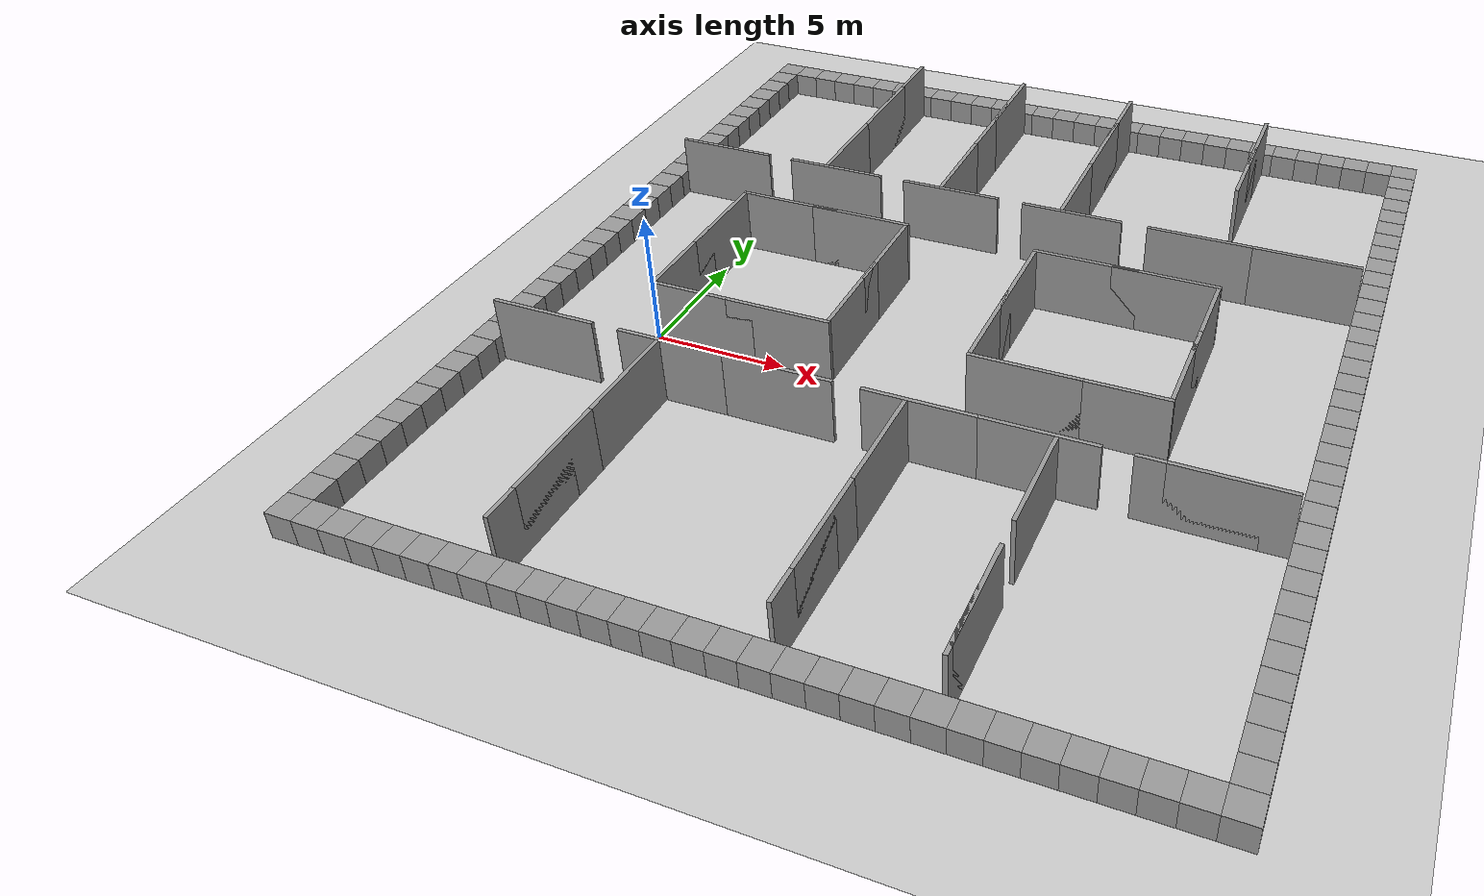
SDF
<sdf version="1.6">
 <world name="default">
  <plugin name="gazebo_occupancy_map" filename="libgazebo_2Dmap_plugin.so">
   <map_resolution>0.05</map_resolution>
   <map_z>0.5</map_z>
   <map_size_x>100</map_size_x>
   <map_size_y>100</map_size_y>
  </plugin>
  <light name="sun" type="directional">
   <pose>0 0 10 0 0 0</pose>
   <diffuse>0.8 0.8 0.8 1</diffuse>
   <specular>0.2 0.2 0.2 1</specular>
   <attenuation>
    <range>1000</range>
    <constant>0.9</constant>
    <linear>0.01</linear>
    <quadratic>0.001</quadratic>
   </attenuation>
   <direction>-0.5 0.1 -0.9</direction>
  </light>
  <model name="ground_plane">
   <static>1</static>
   <link name="link">
    <collision name="collision">
     <geometry><plane><normal>0 0 1</normal><size>100 100</size></plane></geometry>
     <surface><friction><ode><mu>100</mu><mu2>50</mu2></ode></friction></surface>
    </collision>
    <visual name="visual">
     <cast_shadows>0</cast_shadows>
     <geometry><plane><normal>0 0 1</normal><size>100 100</size></plane></geometry>
     <material>
      <script><uri>file://media/materials/scripts/gazebo.material</uri><name>Gazebo/Grey</name></script>
     </material>
    </visual>
    <velocity_decay><linear>0</linear><angular>0</angular></velocity_decay>
   </link>
  </model>
  <physics name="default_physics" default="0" type="ode">
   <max_step_size>0.001</max_step_size>
   <real_time_factor>1</real_time_factor>
   <real_time_update_rate>1000</real_time_update_rate>
  </physics>
  <scene><ambient>0.4 0.4 0.4 1</ambient><background>0.7 0.7 0.7 1</background><shadows>1</shadows></scene>
  <spherical_coordinates>
   <surface_model>EARTH_WGS84</surface_model>
   <latitude_deg>0</latitude_deg>
   <longitude_deg>0</longitude_deg>
   <elevation>0</elevation>
   <heading_deg>0</heading_deg>
  </spherical_coordinates>
  <model name="unit_box_1">
   <pose>-5.0 5.0 0.5 0 0 0</pose>
   <static>1</static>
   <link name="link">
    <inertial>
     <mass>1</mass>
     <inertia><ixx>1</ixx><ixy>0</ixy><ixz>0</ixz><iyy>1</iyy><iyz>0</iyz><izz>1</izz></inertia>
    </inertial>
    <collision name="collision"><geometry><box><size>1 1 1</size></box></geometry></collision>
    <visual name="visual">
     <geometry><box><size>1 1 1</size></box></geometry>
     <material>
      <script><uri>file://media/materials/scripts/gazebo.material</uri><name>Gazebo/Grey</name></script>
     </material>
    </visual>
    <velocity_decay><linear>0</linear><angular>0</angular></velocity_decay>
   </link>
   <static>1</static>
  </model>
  <model name="unit_box_40">
   <pose>-5 4 0.5 0 0 0</pose>
   <static>1</static>
   <link name="link">
    <inertial>
     <mass>1</mass>
     <inertia><ixx>1</ixx><ixy>0</ixy><ixz>0</ixz><iyy>1</iyy><iyz>0</iyz><izz>1</izz></inertia>
    </inertial>
    <collision name="collision"><geometry><box><size>1 1 1</size></box></geometry></collision>
    <visual name="visual">
     <geometry><box><size>1 1 1</size></box></geometry>
     <material>
      <script><uri>file://media/materials/scripts/gazebo.material</uri><name>Gazebo/Grey</name></script>
     </material>
    </visual>
    <velocity_decay><linear>0</linear><angular>0</angular></velocity_decay>
   </link>
   <static>1</static>
  </model>
  <model name="unit_box_41">
   <pose>-5 3 0.5 0 0 0</pose>
   <static>1</static>
   <link name="link">
    <inertial>
     <mass>1</mass>
     <inertia><ixx>1</ixx><ixy>0</ixy><ixz>0</ixz><iyy>1</iyy><iyz>0</iyz><izz>1</izz></inertia>
    </inertial>
    <collision name="collision"><geometry><box><size>1 1 1</size></box></geometry></collision>
    <visual name="visual">
     <geometry><box><size>1 1 1</size></box></geometry>
     <material>
      <script><uri>file://media/materials/scripts/gazebo.material</uri><name>Gazebo/Grey</name></script>
     </material>
    </visual>
    <velocity_decay><linear>0</linear><angular>0</angular></velocity_decay>
   </link>
   <static>1</static>
  </model>
  <model name="unit_box_42">
   <pose>-5 2 0.5 0 0 0</pose>
   <static>1</static>
   <link name="link">
    <inertial>
     <mass>1</mass>
     <inertia><ixx>1</ixx><ixy>0</ixy><ixz>0</ixz><iyy>1</iyy><iyz>0</iyz><izz>1</izz></inertia>
    </inertial>
    <collision name="collision"><geometry><box><size>1 1 1</size></box></geometry></collision>
    <visual name="visual">
     <geometry><box><size>1 1 1</size></box></geometry>
     <material>
      <script><uri>file://media/materials/scripts/gazebo.material</uri><name>Gazebo/Grey</name></script>
     </material>
    </visual>
    <velocity_decay><linear>0</linear><angular>0</angular></velocity_decay>
   </link>
   <static>1</static>
  </model>
  <model name="unit_box_43">
   <pose>-5 1 0.5 0 0 0</pose>
   <static>1</static>
   <link name="link">
    <inertial>
     <mass>1</mass>
     <inertia><ixx>1</ixx><ixy>0</ixy><ixz>0</ixz><iyy>1</iyy><iyz>0</iyz><izz>1</izz></inertia>
    </inertial>
    <collision name="collision"><geometry><box><size>1 1 1</size></box></geometry></collision>
    <visual name="visual">
     <geometry><box><size>1 1 1</size></box></geometry>
     <material>
      <script><uri>file://media/materials/scripts/gazebo.material</uri><name>Gazebo/Grey</name></script>
     </material>
    </visual>
    <velocity_decay><linear>0</linear><angular>0</angular></velocity_decay>
   </link>
   <static>1</static>
  </model>
  <model name="unit_box_44">
   <pose>-5 0 0.5 0 0 0</pose>
   <static>1</static>
   <link name="link">
    <inertial>
     <mass>1</mass>
     <inertia><ixx>1</ixx><ixy>0</ixy><ixz>0</ixz><iyy>1</iyy><iyz>0</iyz><izz>1</izz></inertia>
    </inertial>
    <collision name="collision"><geometry><box><size>1 1 1</size></box></geometry></collision>
    <visual name="visual">
     <geometry><box><size>1 1 1</size></box></geometry>
     <material>
      <script><uri>file://media/materials/scripts/gazebo.material</uri><name>Gazebo/Grey</name></script>
     </material>
    </visual>
    <velocity_decay><linear>0</linear><angular>0</angular></velocity_decay>
   </link>
   <static>1</static>
  </model>
  <model name="unit_box_45">
   <pose>-5 -1 0.5 0 0 0</pose>
   <static>1</static>
   <link name="link">
    <inertial>
     <mass>1</mass>
     <inertia><ixx>1</ixx><ixy>0</ixy><ixz>0</ixz><iyy>1</iyy><iyz>0</iyz><izz>1</izz></inertia>
    </inertial>
    <collision name="collision"><geometry><box><size>1 1 1</size></box></geometry></collision>
    <visual name="visual">
     <geometry><box><size>1 1 1</size></box></geometry>
     <material>
      <script><uri>file://media/materials/scripts/gazebo.material</uri><name>Gazebo/Grey</name></script>
     </material>
    </visual>
    <velocity_decay><linear>0</linear><angular>0</angular></velocity_decay>
   </link>
   <static>1</static>
  </model>
  <model name="unit_box_46">
   <pose>-5 -2 0.5 0 0 0</pose>
   <static>1</static>
   <link name="link">
    <inertial>
     <mass>1</mass>
     <inertia><ixx>1</ixx><ixy>0</ixy><ixz>0</ixz><iyy>1</iyy><iyz>0</iyz><izz>1</izz></inertia>
    </inertial>
    <collision name="collision"><geometry><box><size>1 1 1</size></box></geometry></collision>
    <visual name="visual">
     <geometry><box><size>1 1 1</size></box></geometry>
     <material>
      <script><uri>file://media/materials/scripts/gazebo.material</uri><name>Gazebo/Grey</name></script>
     </material>
    </visual>
    <velocity_decay><linear>0</linear><angular>0</angular></velocity_decay>
   </link>
   <static>1</static>
  </model>
  <model name="unit_box_47">
   <pose>-5 -3 0.5 0 0 0</pose>
   <static>1</static>
   <link name="link">
    <inertial>
     <mass>1</mass>
     <inertia><ixx>1</ixx><ixy>0</ixy><ixz>0</ixz><iyy>1</iyy><iyz>0</iyz><izz>1</izz></inertia>
    </inertial>
    <collision name="collision"><geometry><box><size>1 1 1</size></box></geometry></collision>
    <visual name="visual">
     <geometry><box><size>1 1 1</size></box></geometry>
     <material>
      <script><uri>file://media/materials/scripts/gazebo.material</uri><name>Gazebo/Grey</name></script>
     </material>
    </visual>
    <velocity_decay><linear>0</linear><angular>0</angular></velocity_decay>
   </link>
   <static>1</static>
  </model>
  <model name="unit_box_61">
   <pose>-5 6 0.5 0 0 0</pose>
   <static>1</static>
   <link name="link">
    <inertial>
     <mass>1</mass>
     <inertia><ixx>1</ixx><ixy>0</ixy><ixz>0</ixz><iyy>1</iyy><iyz>0</iyz><izz>1</izz></inertia>
    </inertial>
    <collision name="collision"><geometry><box><size>1 1 1</size></box></geometry></collision>
    <visual name="visual">
     <geometry><box><size>1 1 1</size></box></geometry>
     <material>
      <script><uri>file://media/materials/scripts/gazebo.material</uri><name>Gazebo/Grey</name></script>
     </material>
    </visual>
    <velocity_decay><linear>0</linear><angular>0</angular></velocity_decay>
   </link>
   <static>1</static>
  </model>
  <model name="unit_box_67">
   <pose>-5 7 0.5 0 0 0</pose>
   <static>1</static>
   <link name="link">
    <inertial>
     <mass>1</mass>
     <inertia><ixx>1</ixx><ixy>0</ixy><ixz>0</ixz><iyy>1</iyy><iyz>0</iyz><izz>1</izz></inertia>
    </inertial>
    <collision name="collision"><geometry><box><size>1 1 1</size></box></geometry></collision>
    <visual name="visual">
     <geometry><box><size>1 1 1</size></box></geometry>
     <material>
      <script><uri>file://media/materials/scripts/gazebo.material</uri><name>Gazebo/Grey</name></script>
     </material>
    </visual>
    <velocity_decay><linear>0</linear><angular>0</angular></velocity_decay>
   </link>
   <static>1</static>
  </model>
  <model name="unit_box_68">
   <pose>-5.00001 7.99999 0.5 0 0 8e-06</pose>
   <static>1</static>
   <link name="link">
    <inertial>
     <mass>1</mass>
     <inertia><ixx>1</ixx><ixy>0</ixy><ixz>0</ixz><iyy>1</iyy><iyz>0</iyz><izz>1</izz></inertia>
    </inertial>
    <collision name="collision"><geometry><box><size>1 1 1</size></box></geometry></collision>
    <visual name="visual">
     <geometry><box><size>1 1 1</size></box></geometry>
     <material>
      <script><uri>file://media/materials/scripts/gazebo.material</uri><name>Gazebo/Grey</name></script>
     </material>
    </visual>
    <velocity_decay><linear>0</linear><angular>0</angular></velocity_decay>
   </link>
   <static>1</static>
  </model>
  <model name="unit_box_69">
   <pose>-5 8.99999 0.5 0 0 7e-06</pose>
   <static>1</static>
   <link name="link">
    <inertial>
     <mass>1</mass>
     <inertia><ixx>1</ixx><ixy>0</ixy><ixz>0</ixz><iyy>1</iyy><iyz>0</iyz><izz>1</izz></inertia>
    </inertial>
    <collision name="collision"><geometry><box><size>1 1 1</size></box></geometry></collision>
    <visual name="visual">
     <geometry><box><size>1 1 1</size></box></geometry>
     <material>
      <script><uri>file://media/materials/scripts/gazebo.material</uri><name>Gazebo/Grey</name></script>
     </material>
    </visual>
    <velocity_decay><linear>0</linear><angular>0</angular></velocity_decay>
   </link>
   <static>1</static>
  </model>
  <model name="unit_box_72">
   <pose>-5 10 0.5 0 0 0</pose>
   <static>1</static>
   <link name="link">
    <inertial>
     <mass>1</mass>
     <inertia><ixx>1</ixx><ixy>0</ixy><ixz>0</ixz><iyy>1</iyy><iyz>0</iyz><izz>1</izz></inertia>
    </inertial>
    <collision name="collision"><geometry><box><size>1 1 1</size></box></geometry></collision>
    <visual name="visual">
     <geometry><box><size>1 1 1</size></box></geometry>
     <material>
      <script><uri>file://media/materials/scripts/gazebo.material</uri><name>Gazebo/Grey</name></script>
     </material>
    </visual>
    <velocity_decay><linear>0</linear><angular>0</angular></velocity_decay>
   </link>
   <static>1</static>
  </model>
  <model name="unit_box_73">
   <pose>-5 11 0.5 0 0 0</pose>
   <static>1</static>
   <link name="link">
    <inertial>
     <mass>1</mass>
     <inertia><ixx>1</ixx><ixy>0</ixy><ixz>0</ixz><iyy>1</iyy><iyz>0</iyz><izz>1</izz></inertia>
    </inertial>
    <collision name="collision"><geometry><box><size>1 1 1</size></box></geometry></collision>
    <visual name="visual">
     <geometry><box><size>1 1 1</size></box></geometry>
     <material>
      <script><uri>file://media/materials/scripts/gazebo.material</uri><name>Gazebo/Grey</name></script>
     </material>
    </visual>
    <velocity_decay><linear>0</linear><angular>0</angular></velocity_decay>
   </link>
   <static>1</static>
  </model>
  <model name="unit_box_74">
   <pose>-5.00001 12 0.5 0 0 8e-06</pose>
   <static>1</static>
   <link name="link">
    <inertial>
     <mass>1</mass>
     <inertia><ixx>1</ixx><ixy>0</ixy><ixz>0</ixz><iyy>1</iyy><iyz>0</iyz><izz>1</izz></inertia>
    </inertial>
    <collision name="collision"><geometry><box><size>1 1 1</size></box></geometry></collision>
    <visual name="visual">
     <geometry><box><size>1 1 1</size></box></geometry>
     <material>
      <script><uri>file://media/materials/scripts/gazebo.material</uri><name>Gazebo/Grey</name></script>
     </material>
    </visual>
    <velocity_decay><linear>0</linear><angular>0</angular></velocity_decay>
   </link>
   <static>1</static>
  </model>
  <model name="unit_box_75">
   <pose>-5 13 0.5 0 0 5e-06</pose>
   <static>1</static>
   <link name="link">
    <inertial>
     <mass>1</mass>
     <inertia><ixx>1</ixx><ixy>0</ixy><ixz>0</ixz><iyy>1</iyy><iyz>0</iyz><izz>1</izz></inertia>
    </inertial>
    <collision name="collision"><geometry><box><size>1 1 1</size></box></geometry></collision>
    <visual name="visual">
     <geometry><box><size>1 1 1</size></box></geometry>
     <material>
      <script><uri>file://media/materials/scripts/gazebo.material</uri><name>Gazebo/Grey</name></script>
     </material>
    </visual>
    <velocity_decay><linear>0</linear><angular>0</angular></velocity_decay>
   </link>
   <static>1</static>
  </model>
  <model name="unit_box_76">
   <pose>-5 14 0.5 0 0 6e-06</pose>
   <static>1</static>
   <link name="link">
    <inertial>
     <mass>1</mass>
     <inertia><ixx>1</ixx><ixy>0</ixy><ixz>0</ixz><iyy>1</iyy><iyz>0</iyz><izz>1</izz></inertia>
    </inertial>
    <collision name="collision"><geometry><box><size>1 1 1</size></box></geometry></collision>
    <visual name="visual">
     <geometry><box><size>1 1 1</size></box></geometry>
     <material>
      <script><uri>file://media/materials/scripts/gazebo.material</uri><name>Gazebo/Grey</name></script>
     </material>
    </visual>
    <velocity_decay><linear>0</linear><angular>0</angular></velocity_decay>
   </link>
   <static>1</static>
  </model>
  <model name="unit_box_77">
   <pose>-4.99999 15 0.5 0 0 7e-06</pose>
   <static>1</static>
   <link name="link">
    <inertial>
     <mass>1</mass>
     <inertia><ixx>1</ixx><ixy>0</ixy><ixz>0</ixz><iyy>1</iyy><iyz>0</iyz><izz>1</izz></inertia>
    </inertial>
    <collision name="collision"><geometry><box><size>1 1 1</size></box></geometry></collision>
    <visual name="visual">
     <geometry><box><size>1 1 1</size></box></geometry>
     <material>
      <script><uri>file://media/materials/scripts/gazebo.material</uri><name>Gazebo/Grey</name></script>
     </material>
    </visual>
    <velocity_decay><linear>0</linear><angular>0</angular></velocity_decay>
   </link>
   <static>1</static>
  </model>
  <model name="unit_box_78">
   <pose>-5 16 0.5 0 0 7e-06</pose>
   <static>1</static>
   <link name="link">
    <inertial>
     <mass>1</mass>
     <inertia><ixx>1</ixx><ixy>0</ixy><ixz>0</ixz><iyy>1</iyy><iyz>0</iyz><izz>1</izz></inertia>
    </inertial>
    <collision name="collision"><geometry><box><size>1 1 1</size></box></geometry></collision>
    <visual name="visual">
     <geometry><box><size>1 1 1</size></box></geometry>
     <material>
      <script><uri>file://media/materials/scripts/gazebo.material</uri><name>Gazebo/Grey</name></script>
     </material>
    </visual>
    <velocity_decay><linear>0</linear><angular>0</angular></velocity_decay>
   </link>
   <static>1</static>
  </model>
  <model name="unit_box_79">
   <pose>-4.99997 17 0.5 0 0 6e-06</pose>
   <static>1</static>
   <link name="link">
    <inertial>
     <mass>1</mass>
     <inertia><ixx>1</ixx><ixy>0</ixy><ixz>0</ixz><iyy>1</iyy><iyz>0</iyz><izz>1</izz></inertia>
    </inertial>
    <collision name="collision"><geometry><box><size>1 1 1</size></box></geometry></collision>
    <visual name="visual">
     <geometry><box><size>1 1 1</size></box></geometry>
     <material>
      <script><uri>file://media/materials/scripts/gazebo.material</uri><name>Gazebo/Grey</name></script>
     </material>
    </visual>
    <velocity_decay><linear>0</linear><angular>0</angular></velocity_decay>
   </link>
   <static>1</static>
  </model>
  <model name="unit_box_80">
   <pose>-5 18 0.5 0 0 0</pose>
   <static>1</static>
   <link name="link">
    <inertial>
     <mass>1</mass>
     <inertia><ixx>1</ixx><ixy>0</ixy><ixz>0</ixz><iyy>1</iyy><iyz>0</iyz><izz>1</izz></inertia>
    </inertial>
    <collision name="collision"><geometry><box><size>1 1 1</size></box></geometry></collision>
    <visual name="visual">
     <geometry><box><size>1 1 1</size></box></geometry>
     <material>
      <script><uri>file://media/materials/scripts/gazebo.material</uri><name>Gazebo/Grey</name></script>
     </material>
    </visual>
    <velocity_decay><linear>0</linear><angular>0</angular></velocity_decay>
   </link>
   <static>1</static>
  </model>
  <model name="unit_box_96">
   <pose>-5 19 0.5 0 0 0</pose>
   <static>1</static>
   <link name="link">
    <inertial>
     <mass>1</mass>
     <inertia><ixx>1</ixx><ixy>0</ixy><ixz>0</ixz><iyy>1</iyy><iyz>0</iyz><izz>1</izz></inertia>
    </inertial>
    <collision name="collision"><geometry><box><size>1 1 1</size></box></geometry></collision>
    <visual name="visual">
     <geometry><box><size>1 1 1</size></box></geometry>
     <material>
      <script><uri>file://media/materials/scripts/gazebo.material</uri><name>Gazebo/Grey</name></script>
     </material>
    </visual>
    <velocity_decay><linear>0</linear><angular>0</angular></velocity_decay>
   </link>
   <static>1</static>
  </model>
  <model name="unit_box_97">
   <pose>-4.99997 20 0.5 0 0 1e-06</pose>
   <static>1</static>
   <link name="link">
    <inertial>
     <mass>1</mass>
     <inertia><ixx>1</ixx><ixy>0</ixy><ixz>0</ixz><iyy>1</iyy><iyz>0</iyz><izz>1</izz></inertia>
    </inertial>
    <collision name="collision"><geometry><box><size>1 1 1</size></box></geometry></collision>
    <visual name="visual">
     <geometry><box><size>1 1 1</size></box></geometry>
     <material>
      <script><uri>file://media/materials/scripts/gazebo.material</uri><name>Gazebo/Grey</name></script>
     </material>
    </visual>
    <velocity_decay><linear>0</linear><angular>0</angular></velocity_decay>
   </link>
   <static>1</static>
  </model>
  <model name="unit_box_98">
   <pose>-5.00001 21 0.5 0 0 0</pose>
   <static>1</static>
   <link name="link">
    <inertial>
     <mass>1</mass>
     <inertia><ixx>1</ixx><ixy>0</ixy><ixz>0</ixz><iyy>1</iyy><iyz>0</iyz><izz>1</izz></inertia>
    </inertial>
    <collision name="collision"><geometry><box><size>1 1 1</size></box></geometry></collision>
    <visual name="visual">
     <geometry><box><size>1 1 1</size></box></geometry>
     <material>
      <script><uri>file://media/materials/scripts/gazebo.material</uri><name>Gazebo/Grey</name></script>
     </material>
    </visual>
    <velocity_decay><linear>0</linear><angular>0</angular></velocity_decay>
   </link>
   <static>1</static>
  </model>
  <model name="unit_box_99">
   <pose>-4.00001 21 0.5 0 0 -1e-06</pose>
   <static>1</static>
   <link name="link">
    <inertial>
     <mass>1</mass>
     <inertia><ixx>1</ixx><ixy>0</ixy><ixz>0</ixz><iyy>1</iyy><iyz>0</iyz><izz>1</izz></inertia>
    </inertial>
    <collision name="collision"><geometry><box><size>1 1 1</size></box></geometry></collision>
    <visual name="visual">
     <geometry><box><size>1 1 1</size></box></geometry>
     <material>
      <script><uri>file://media/materials/scripts/gazebo.material</uri><name>Gazebo/Grey</name></script>
     </material>
    </visual>
    <velocity_decay><linear>0</linear><angular>0</angular></velocity_decay>
   </link>
   <static>1</static>
  </model>
  <model name="unit_box_100">
   <pose>-3.0 21 0.5 0 0 0</pose>
   <static>1</static>
   <link name="link">
    <inertial>
     <mass>1</mass>
     <inertia><ixx>1</ixx><ixy>0</ixy><ixz>0</ixz><iyy>1</iyy><iyz>0</iyz><izz>1</izz></inertia>
    </inertial>
    <collision name="collision"><geometry><box><size>1 1 1</size></box></geometry></collision>
    <visual name="visual">
     <geometry><box><size>1 1 1</size></box></geometry>
     <material>
      <script><uri>file://media/materials/scripts/gazebo.material</uri><name>Gazebo/Grey</name></script>
     </material>
    </visual>
    <velocity_decay><linear>0</linear><angular>0</angular></velocity_decay>
   </link>
   <static>1</static>
  </model>
  <model name="unit_box_101">
   <pose>-2.0 21 0.5 0 0 0</pose>
   <static>1</static>
   <link name="link">
    <inertial>
     <mass>1</mass>
     <inertia><ixx>1</ixx><ixy>0</ixy><ixz>0</ixz><iyy>1</iyy><iyz>0</iyz><izz>1</izz></inertia>
    </inertial>
    <collision name="collision"><geometry><box><size>1 1 1</size></box></geometry></collision>
    <visual name="visual">
     <geometry><box><size>1 1 1</size></box></geometry>
     <material>
      <script><uri>file://media/materials/scripts/gazebo.material</uri><name>Gazebo/Grey</name></script>
     </material>
    </visual>
    <velocity_decay><linear>0</linear><angular>0</angular></velocity_decay>
   </link>
   <static>1</static>
  </model>
  <model name="unit_box_102">
   <pose>-1.0 21 0.5 0 0 0</pose>
   <static>1</static>
   <link name="link">
    <inertial>
     <mass>1</mass>
     <inertia><ixx>1</ixx><ixy>0</ixy><ixz>0</ixz><iyy>1</iyy><iyz>0</iyz><izz>1</izz></inertia>
    </inertial>
    <collision name="collision"><geometry><box><size>1 1 1</size></box></geometry></collision>
    <visual name="visual">
     <geometry><box><size>1 1 1</size></box></geometry>
     <material>
      <script><uri>file://media/materials/scripts/gazebo.material</uri><name>Gazebo/Grey</name></script>
     </material>
    </visual>
    <velocity_decay><linear>0</linear><angular>0</angular></velocity_decay>
   </link>
   <static>1</static>
  </model>
  <model name="unit_box_103">
   <pose>-1e-05 21 0.5 0 0 0</pose>
   <static>1</static>
   <link name="link">
    <inertial>
     <mass>1</mass>
     <inertia><ixx>1</ixx><ixy>0</ixy><ixz>0</ixz><iyy>1</iyy><iyz>0</iyz><izz>1</izz></inertia>
    </inertial>
    <collision name="collision"><geometry><box><size>1 1 1</size></box></geometry></collision>
    <visual name="visual">
     <geometry><box><size>1 1 1</size></box></geometry>
     <material>
      <script><uri>file://media/materials/scripts/gazebo.material</uri><name>Gazebo/Grey</name></script>
     </material>
    </visual>
    <velocity_decay><linear>0</linear><angular>0</angular></velocity_decay>
   </link>
   <static>1</static>
  </model>
  <model name="unit_box_104">
   <pose>1 21 0.5 0 0 0</pose>
   <static>1</static>
   <link name="link">
    <inertial>
     <mass>1</mass>
     <inertia><ixx>1</ixx><ixy>0</ixy><ixz>0</ixz><iyy>1</iyy><iyz>0</iyz><izz>1</izz></inertia>
    </inertial>
    <collision name="collision"><geometry><box><size>1 1 1</size></box></geometry></collision>
    <visual name="visual">
     <geometry><box><size>1 1 1</size></box></geometry>
     <material>
      <script><uri>file://media/materials/scripts/gazebo.material</uri><name>Gazebo/Grey</name></script>
     </material>
    </visual>
    <velocity_decay><linear>0</linear><angular>0</angular></velocity_decay>
   </link>
   <static>1</static>
  </model>
  <model name="unit_box_105">
   <pose>1.99999 21 0.5 0 0 0</pose>
   <static>1</static>
   <link name="link">
    <inertial>
     <mass>1</mass>
     <inertia><ixx>1</ixx><ixy>0</ixy><ixz>0</ixz><iyy>1</iyy><iyz>0</iyz><izz>1</izz></inertia>
    </inertial>
    <collision name="collision"><geometry><box><size>1 1 1</size></box></geometry></collision>
    <visual name="visual">
     <geometry><box><size>1 1 1</size></box></geometry>
     <material>
      <script><uri>file://media/materials/scripts/gazebo.material</uri><name>Gazebo/Grey</name></script>
     </material>
    </visual>
    <velocity_decay><linear>0</linear><angular>0</angular></velocity_decay>
   </link>
   <static>1</static>
  </model>
  <model name="unit_box_106">
   <pose>2.99999 21 0.5 0 0 1e-06</pose>
   <static>1</static>
   <link name="link">
    <inertial>
     <mass>1</mass>
     <inertia><ixx>1</ixx><ixy>0</ixy><ixz>0</ixz><iyy>1</iyy><iyz>0</iyz><izz>1</izz></inertia>
    </inertial>
    <collision name="collision"><geometry><box><size>1 1 1</size></box></geometry></collision>
    <visual name="visual">
     <geometry><box><size>1 1 1</size></box></geometry>
     <material>
      <script><uri>file://media/materials/scripts/gazebo.material</uri><name>Gazebo/Grey</name></script>
     </material>
    </visual>
    <velocity_decay><linear>0</linear><angular>0</angular></velocity_decay>
   </link>
   <static>1</static>
  </model>
  <model name="unit_box_107">
   <pose>3.99999 21 0.5 0 0 2e-06</pose>
   <static>1</static>
   <link name="link">
    <inertial>
     <mass>1</mass>
     <inertia><ixx>1</ixx><ixy>0</ixy><ixz>0</ixz><iyy>1</iyy><iyz>0</iyz><izz>1</izz></inertia>
    </inertial>
    <collision name="collision"><geometry><box><size>1 1 1</size></box></geometry></collision>
    <visual name="visual">
     <geometry><box><size>1 1 1</size></box></geometry>
     <material>
      <script><uri>file://media/materials/scripts/gazebo.material</uri><name>Gazebo/Grey</name></script>
     </material>
    </visual>
    <velocity_decay><linear>0</linear><angular>0</angular></velocity_decay>
   </link>
   <static>1</static>
  </model>
  <model name="unit_box_108">
   <pose>5 21 0.5 0 0 3e-06</pose>
   <static>1</static>
   <link name="link">
    <inertial>
     <mass>1</mass>
     <inertia><ixx>1</ixx><ixy>0</ixy><ixz>0</ixz><iyy>1</iyy><iyz>0</iyz><izz>1</izz></inertia>
    </inertial>
    <collision name="collision"><geometry><box><size>1 1 1</size></box></geometry></collision>
    <visual name="visual">
     <geometry><box><size>1 1 1</size></box></geometry>
     <material>
      <script><uri>file://media/materials/scripts/gazebo.material</uri><name>Gazebo/Grey</name></script>
     </material>
    </visual>
    <velocity_decay><linear>0</linear><angular>0</angular></velocity_decay>
   </link>
   <static>1</static>
  </model>
  <model name="unit_box_109">
   <pose>6 20.9999 0.5 0 0 3e-06</pose>
   <static>1</static>
   <link name="link">
    <inertial>
     <mass>1</mass>
     <inertia><ixx>1</ixx><ixy>0</ixy><ixz>0</ixz><iyy>1</iyy><iyz>0</iyz><izz>1</izz></inertia>
    </inertial>
    <collision name="collision"><geometry><box><size>1 1 1</size></box></geometry></collision>
    <visual name="visual">
     <geometry><box><size>1 1 1</size></box></geometry>
     <material>
      <script><uri>file://media/materials/scripts/gazebo.material</uri><name>Gazebo/Grey</name></script>
     </material>
    </visual>
    <velocity_decay><linear>0</linear><angular>0</angular></velocity_decay>
   </link>
   <static>1</static>
  </model>
  <model name="unit_box_110">
   <pose>7 21 0.5 0 0 4e-06</pose>
   <static>1</static>
   <link name="link">
    <inertial>
     <mass>1</mass>
     <inertia><ixx>1</ixx><ixy>0</ixy><ixz>0</ixz><iyy>1</iyy><iyz>0</iyz><izz>1</izz></inertia>
    </inertial>
    <collision name="collision"><geometry><box><size>1 1 1</size></box></geometry></collision>
    <visual name="visual">
     <geometry><box><size>1 1 1</size></box></geometry>
     <material>
      <script><uri>file://media/materials/scripts/gazebo.material</uri><name>Gazebo/Grey</name></script>
     </material>
    </visual>
    <velocity_decay><linear>0</linear><angular>0</angular></velocity_decay>
   </link>
   <static>1</static>
  </model>
  <model name="unit_box_111">
   <pose>8 21 0.5 0 0 3e-06</pose>
   <static>1</static>
   <link name="link">
    <inertial>
     <mass>1</mass>
     <inertia><ixx>1</ixx><ixy>0</ixy><ixz>0</ixz><iyy>1</iyy><iyz>0</iyz><izz>1</izz></inertia>
    </inertial>
    <collision name="collision"><geometry><box><size>1 1 1</size></box></geometry></collision>
    <visual name="visual">
     <geometry><box><size>1 1 1</size></box></geometry>
     <material>
      <script><uri>file://media/materials/scripts/gazebo.material</uri><name>Gazebo/Grey</name></script>
     </material>
    </visual>
    <velocity_decay><linear>0</linear><angular>0</angular></velocity_decay>
   </link>
   <static>1</static>
  </model>
  <model name="unit_box_112">
   <pose>9 21 0.5 0 0 3e-06</pose>
   <static>1</static>
   <link name="link">
    <inertial>
     <mass>1</mass>
     <inertia><ixx>1</ixx><ixy>0</ixy><ixz>0</ixz><iyy>1</iyy><iyz>0</iyz><izz>1</izz></inertia>
    </inertial>
    <collision name="collision"><geometry><box><size>1 1 1</size></box></geometry></collision>
    <visual name="visual">
     <geometry><box><size>1 1 1</size></box></geometry>
     <material>
      <script><uri>file://media/materials/scripts/gazebo.material</uri><name>Gazebo/Grey</name></script>
     </material>
    </visual>
    <velocity_decay><linear>0</linear><angular>0</angular></velocity_decay>
   </link>
   <static>1</static>
  </model>
  <model name="unit_box_113">
   <pose>10 21 0.5 0 0 1e-06</pose>
   <static>1</static>
   <link name="link">
    <inertial>
     <mass>1</mass>
     <inertia><ixx>1</ixx><ixy>0</ixy><ixz>0</ixz><iyy>1</iyy><iyz>0</iyz><izz>1</izz></inertia>
    </inertial>
    <collision name="collision"><geometry><box><size>1 1 1</size></box></geometry></collision>
    <visual name="visual">
     <geometry><box><size>1 1 1</size></box></geometry>
     <material>
      <script><uri>file://media/materials/scripts/gazebo.material</uri><name>Gazebo/Grey</name></script>
     </material>
    </visual>
    <velocity_decay><linear>0</linear><angular>0</angular></velocity_decay>
   </link>
   <static>1</static>
  </model>
  <model name="unit_box_114">
   <pose>11 21 0.5 0 0 1e-06</pose>
   <static>1</static>
   <link name="link">
    <inertial>
     <mass>1</mass>
     <inertia><ixx>1</ixx><ixy>0</ixy><ixz>0</ixz><iyy>1</iyy><iyz>0</iyz><izz>1</izz></inertia>
    </inertial>
    <collision name="collision"><geometry><box><size>1 1 1</size></box></geometry></collision>
    <visual name="visual">
     <geometry><box><size>1 1 1</size></box></geometry>
     <material>
      <script><uri>file://media/materials/scripts/gazebo.material</uri><name>Gazebo/Grey</name></script>
     </material>
    </visual>
    <velocity_decay><linear>0</linear><angular>0</angular></velocity_decay>
   </link>
   <static>1</static>
  </model>
  <model name="unit_box_115">
   <pose>12 21 0.5 0 0 -2e-06</pose>
   <static>1</static>
   <link name="link">
    <inertial>
     <mass>1</mass>
     <inertia><ixx>1</ixx><ixy>0</ixy><ixz>0</ixz><iyy>1</iyy><iyz>0</iyz><izz>1</izz></inertia>
    </inertial>
    <collision name="collision"><geometry><box><size>1 1 1</size></box></geometry></collision>
    <visual name="visual">
     <geometry><box><size>1 1 1</size></box></geometry>
     <material>
      <script><uri>file://media/materials/scripts/gazebo.material</uri><name>Gazebo/Grey</name></script>
     </material>
    </visual>
    <velocity_decay><linear>0</linear><angular>0</angular></velocity_decay>
   </link>
   <static>1</static>
  </model>
  <model name="unit_box_116">
   <pose>13 21 0.5 0 0 -2e-06</pose>
   <static>1</static>
   <link name="link">
    <inertial>
     <mass>1</mass>
     <inertia><ixx>1</ixx><ixy>0</ixy><ixz>0</ixz><iyy>1</iyy><iyz>0</iyz><izz>1</izz></inertia>
    </inertial>
    <collision name="collision"><geometry><box><size>1 1 1</size></box></geometry></collision>
    <visual name="visual">
     <geometry><box><size>1 1 1</size></box></geometry>
     <material>
      <script><uri>file://media/materials/scripts/gazebo.material</uri><name>Gazebo/Grey</name></script>
     </material>
    </visual>
    <velocity_decay><linear>0</linear><angular>0</angular></velocity_decay>
   </link>
   <static>1</static>
  </model>
  <model name="unit_box_121">
   <pose>14 21 0.5 0 0 -2e-06</pose>
   <static>1</static>
   <link name="link">
    <inertial>
     <mass>1</mass>
     <inertia><ixx>1</ixx><ixy>0</ixy><ixz>0</ixz><iyy>1</iyy><iyz>0</iyz><izz>1</izz></inertia>
    </inertial>
    <collision name="collision"><geometry><box><size>1 1 1</size></box></geometry></collision>
    <visual name="visual">
     <geometry><box><size>1 1 1</size></box></geometry>
     <material>
      <script><uri>file://media/materials/scripts/gazebo.material</uri><name>Gazebo/Grey</name></script>
     </material>
    </visual>
    <velocity_decay><linear>0</linear><angular>0</angular></velocity_decay>
   </link>
   <static>1</static>
  </model>
  <model name="unit_box_134">
   <pose>15 21 0.5 0 0 1e-06</pose>
   <static>1</static>
   <link name="link">
    <inertial>
     <mass>1</mass>
     <inertia><ixx>1</ixx><ixy>0</ixy><ixz>0</ixz><iyy>1</iyy><iyz>0</iyz><izz>1</izz></inertia>
    </inertial>
    <collision name="collision"><geometry><box><size>1 1 1</size></box></geometry></collision>
    <visual name="visual">
     <geometry><box><size>1 1 1</size></box></geometry>
     <material>
      <script><uri>file://media/materials/scripts/gazebo.material</uri><name>Gazebo/Grey</name></script>
     </material>
    </visual>
    <velocity_decay><linear>0</linear><angular>0</angular></velocity_decay>
   </link>
   <static>1</static>
  </model>
  <model name="unit_box_135">
   <pose>16 21 0.5 0 0 1e-06</pose>
   <static>1</static>
   <link name="link">
    <inertial>
     <mass>1</mass>
     <inertia><ixx>1</ixx><ixy>0</ixy><ixz>0</ixz><iyy>1</iyy><iyz>0</iyz><izz>1</izz></inertia>
    </inertial>
    <collision name="collision"><geometry><box><size>1 1 1</size></box></geometry></collision>
    <visual name="visual">
     <geometry><box><size>1 1 1</size></box></geometry>
     <material>
      <script><uri>file://media/materials/scripts/gazebo.material</uri><name>Gazebo/Grey</name></script>
     </material>
    </visual>
    <velocity_decay><linear>0</linear><angular>0</angular></velocity_decay>
   </link>
   <static>1</static>
  </model>
  <model name="unit_box_136">
   <pose>17 21 0.5 0 0 3e-06</pose>
   <static>1</static>
   <link name="link">
    <inertial>
     <mass>1</mass>
     <inertia><ixx>1</ixx><ixy>0</ixy><ixz>0</ixz><iyy>1</iyy><iyz>0</iyz><izz>1</izz></inertia>
    </inertial>
    <collision name="collision"><geometry><box><size>1 1 1</size></box></geometry></collision>
    <visual name="visual">
     <geometry><box><size>1 1 1</size></box></geometry>
     <material>
      <script><uri>file://media/materials/scripts/gazebo.material</uri><name>Gazebo/Grey</name></script>
     </material>
    </visual>
    <velocity_decay><linear>0</linear><angular>0</angular></velocity_decay>
   </link>
   <static>1</static>
  </model>
  <model name="unit_box_137">
   <pose>18 21 0.5 0 0 3e-06</pose>
   <static>1</static>
   <link name="link">
    <inertial>
     <mass>1</mass>
     <inertia><ixx>1</ixx><ixy>0</ixy><ixz>0</ixz><iyy>1</iyy><iyz>0</iyz><izz>1</izz></inertia>
    </inertial>
    <collision name="collision"><geometry><box><size>1 1 1</size></box></geometry></collision>
    <visual name="visual">
     <geometry><box><size>1 1 1</size></box></geometry>
     <material>
      <script><uri>file://media/materials/scripts/gazebo.material</uri><name>Gazebo/Grey</name></script>
     </material>
    </visual>
    <velocity_decay><linear>0</linear><angular>0</angular></velocity_decay>
   </link>
   <static>1</static>
  </model>
  <model name="unit_box_146">
   <pose>19 21 0.5 0 0 3e-06</pose>
   <static>1</static>
   <link name="link">
    <inertial>
     <mass>1</mass>
     <inertia><ixx>1</ixx><ixy>0</ixy><ixz>0</ixz><iyy>1</iyy><iyz>0</iyz><izz>1</izz></inertia>
    </inertial>
    <collision name="collision"><geometry><box><size>1 1 1</size></box></geometry></collision>
    <visual name="visual">
     <geometry><box><size>1 1 1</size></box></geometry>
     <material>
      <script><uri>file://media/materials/scripts/gazebo.material</uri><name>Gazebo/Grey</name></script>
     </material>
    </visual>
    <velocity_decay><linear>0</linear><angular>0</angular></velocity_decay>
   </link>
   <static>1</static>
  </model>
  <model name="unit_box_147">
   <pose>20.0003 21 0.5 0 0 1.4e-05</pose>
   <static>1</static>
   <link name="link">
    <inertial>
     <mass>1</mass>
     <inertia><ixx>1</ixx><ixy>0</ixy><ixz>0</ixz><iyy>1</iyy><iyz>0</iyz><izz>1</izz></inertia>
    </inertial>
    <collision name="collision"><geometry><box><size>1 1 1</size></box></geometry></collision>
    <visual name="visual">
     <geometry><box><size>1 1 1</size></box></geometry>
     <material>
      <script><uri>file://media/materials/scripts/gazebo.material</uri><name>Gazebo/Grey</name></script>
     </material>
    </visual>
    <velocity_decay><linear>0</linear><angular>0</angular></velocity_decay>
   </link>
   <static>1</static>
  </model>
  <model name="unit_box_148">
   <pose>21.0003 21 0.5 0 0 3.3e-05</pose>
   <static>1</static>
   <link name="link">
    <inertial>
     <mass>1</mass>
     <inertia><ixx>1</ixx><ixy>0</ixy><ixz>0</ixz><iyy>1</iyy><iyz>0</iyz><izz>1</izz></inertia>
    </inertial>
    <collision name="collision"><geometry><box><size>1 1 1</size></box></geometry></collision>
    <visual name="visual">
     <geometry><box><size>1 1 1</size></box></geometry>
     <material>
      <script><uri>file://media/materials/scripts/gazebo.material</uri><name>Gazebo/Grey</name></script>
     </material>
    </visual>
    <velocity_decay><linear>0</linear><angular>0</angular></velocity_decay>
   </link>
   <static>1</static>
  </model>
  <model name="unit_box_150">
   <pose>22.0003 21.0001 0.5 0 0 7.3e-05</pose>
   <static>1</static>
   <link name="link">
    <inertial>
     <mass>1</mass>
     <inertia><ixx>1</ixx><ixy>0</ixy><ixz>0</ixz><iyy>1</iyy><iyz>0</iyz><izz>1</izz></inertia>
    </inertial>
    <collision name="collision"><geometry><box><size>1 1 1</size></box></geometry></collision>
    <visual name="visual">
     <geometry><box><size>1 1 1</size></box></geometry>
     <material>
      <script><uri>file://media/materials/scripts/gazebo.material</uri><name>Gazebo/Grey</name></script>
     </material>
    </visual>
    <velocity_decay><linear>0</linear><angular>0</angular></velocity_decay>
   </link>
   <static>1</static>
  </model>
  <model name="unit_box_151">
   <pose>23.0004 21.0004 0.5 0 0 0.000111</pose>
   <static>1</static>
   <link name="link">
    <inertial>
     <mass>1</mass>
     <inertia><ixx>1</ixx><ixy>0</ixy><ixz>0</ixz><iyy>1</iyy><iyz>0</iyz><izz>1</izz></inertia>
    </inertial>
    <collision name="collision"><geometry><box><size>1 1 1</size></box></geometry></collision>
    <visual name="visual">
     <geometry><box><size>1 1 1</size></box></geometry>
     <material>
      <script><uri>file://media/materials/scripts/gazebo.material</uri><name>Gazebo/Grey</name></script>
     </material>
    </visual>
    <velocity_decay><linear>0</linear><angular>0</angular></velocity_decay>
   </link>
   <static>1</static>
  </model>
  <model name="unit_box_152">
   <pose>24.0004 21.0005 0.5 0 0 4.7e-05</pose>
   <static>1</static>
   <link name="link">
    <inertial>
     <mass>1</mass>
     <inertia><ixx>1</ixx><ixy>0</ixy><ixz>0</ixz><iyy>1</iyy><iyz>0</iyz><izz>1</izz></inertia>
    </inertial>
    <collision name="collision"><geometry><box><size>1 1 1</size></box></geometry></collision>
    <visual name="visual">
     <geometry><box><size>1 1 1</size></box></geometry>
     <material>
      <script><uri>file://media/materials/scripts/gazebo.material</uri><name>Gazebo/Grey</name></script>
     </material>
    </visual>
    <velocity_decay><linear>0</linear><angular>0</angular></velocity_decay>
   </link>
   <static>1</static>
  </model>
  <model name="unit_box_153">
   <pose>24.0001 20.0005 0.5 0 0 2.5e-05</pose>
   <static>1</static>
   <link name="link">
    <inertial>
     <mass>1</mass>
     <inertia><ixx>1</ixx><ixy>0</ixy><ixz>0</ixz><iyy>1</iyy><iyz>0</iyz><izz>1</izz></inertia>
    </inertial>
    <collision name="collision"><geometry><box><size>1 1 1</size></box></geometry></collision>
    <visual name="visual">
     <geometry><box><size>1 1 1</size></box></geometry>
     <material>
      <script><uri>file://media/materials/scripts/gazebo.material</uri><name>Gazebo/Grey</name></script>
     </material>
    </visual>
    <velocity_decay><linear>0</linear><angular>0</angular></velocity_decay>
   </link>
   <static>1</static>
  </model>
  <model name="unit_box_154">
   <pose>24.0001 19.0005 0.5 0 0 1.7e-05</pose>
   <static>1</static>
   <link name="link">
    <inertial>
     <mass>1</mass>
     <inertia><ixx>1</ixx><ixy>0</ixy><ixz>0</ixz><iyy>1</iyy><iyz>0</iyz><izz>1</izz></inertia>
    </inertial>
    <collision name="collision"><geometry><box><size>1 1 1</size></box></geometry></collision>
    <visual name="visual">
     <geometry><box><size>1 1 1</size></box></geometry>
     <material>
      <script><uri>file://media/materials/scripts/gazebo.material</uri><name>Gazebo/Grey</name></script>
     </material>
    </visual>
    <velocity_decay><linear>0</linear><angular>0</angular></velocity_decay>
   </link>
   <static>1</static>
  </model>
  <model name="unit_box_155">
   <pose>24.0001 18.0005 0.5 0 0 1.3e-05</pose>
   <static>1</static>
   <link name="link">
    <inertial>
     <mass>1</mass>
     <inertia><ixx>1</ixx><ixy>0</ixy><ixz>0</ixz><iyy>1</iyy><iyz>0</iyz><izz>1</izz></inertia>
    </inertial>
    <collision name="collision"><geometry><box><size>1 1 1</size></box></geometry></collision>
    <visual name="visual">
     <geometry><box><size>1 1 1</size></box></geometry>
     <material>
      <script><uri>file://media/materials/scripts/gazebo.material</uri><name>Gazebo/Grey</name></script>
     </material>
    </visual>
    <velocity_decay><linear>0</linear><angular>0</angular></velocity_decay>
   </link>
   <static>1</static>
  </model>
  <model name="unit_box_156">
   <pose>24.0001 17.0005 0.5 0 0 1.4e-05</pose>
   <static>1</static>
   <link name="link">
    <inertial>
     <mass>1</mass>
     <inertia><ixx>1</ixx><ixy>0</ixy><ixz>0</ixz><iyy>1</iyy><iyz>0</iyz><izz>1</izz></inertia>
    </inertial>
    <collision name="collision"><geometry><box><size>1 1 1</size></box></geometry></collision>
    <visual name="visual">
     <geometry><box><size>1 1 1</size></box></geometry>
     <material>
      <script><uri>file://media/materials/scripts/gazebo.material</uri><name>Gazebo/Grey</name></script>
     </material>
    </visual>
    <velocity_decay><linear>0</linear><angular>0</angular></velocity_decay>
   </link>
   <static>1</static>
  </model>
  <model name="unit_box_157">
   <pose>24.0002 16.0005 0.5 0 0 1.5e-05</pose>
   <static>1</static>
   <link name="link">
    <inertial>
     <mass>1</mass>
     <inertia><ixx>1</ixx><ixy>0</ixy><ixz>0</ixz><iyy>1</iyy><iyz>0</iyz><izz>1</izz></inertia>
    </inertial>
    <collision name="collision"><geometry><box><size>1 1 1</size></box></geometry></collision>
    <visual name="visual">
     <geometry><box><size>1 1 1</size></box></geometry>
     <material>
      <script><uri>file://media/materials/scripts/gazebo.material</uri><name>Gazebo/Grey</name></script>
     </material>
    </visual>
    <velocity_decay><linear>0</linear><angular>0</angular></velocity_decay>
   </link>
   <static>1</static>
  </model>
  <model name="unit_box_158">
   <pose>24.0001 15.0005 0.5 0 0 1.7e-05</pose>
   <static>1</static>
   <link name="link">
    <inertial>
     <mass>1</mass>
     <inertia><ixx>1</ixx><ixy>0</ixy><ixz>0</ixz><iyy>1</iyy><iyz>0</iyz><izz>1</izz></inertia>
    </inertial>
    <collision name="collision"><geometry><box><size>1 1 1</size></box></geometry></collision>
    <visual name="visual">
     <geometry><box><size>1 1 1</size></box></geometry>
     <material>
      <script><uri>file://media/materials/scripts/gazebo.material</uri><name>Gazebo/Grey</name></script>
     </material>
    </visual>
    <velocity_decay><linear>0</linear><angular>0</angular></velocity_decay>
   </link>
   <static>1</static>
  </model>
  <model name="unit_box_159">
   <pose>24 14.0005 0.5 0 0 2e-05</pose>
   <static>1</static>
   <link name="link">
    <inertial>
     <mass>1</mass>
     <inertia><ixx>1</ixx><ixy>0</ixy><ixz>0</ixz><iyy>1</iyy><iyz>0</iyz><izz>1</izz></inertia>
    </inertial>
    <collision name="collision"><geometry><box><size>1 1 1</size></box></geometry></collision>
    <visual name="visual">
     <geometry><box><size>1 1 1</size></box></geometry>
     <material>
      <script><uri>file://media/materials/scripts/gazebo.material</uri><name>Gazebo/Grey</name></script>
     </material>
    </visual>
    <velocity_decay><linear>0</linear><angular>0</angular></velocity_decay>
   </link>
   <static>1</static>
  </model>
  <model name="unit_box_160">
   <pose>24 13.0005 0.5 0 0 2.1e-05</pose>
   <static>1</static>
   <link name="link">
    <inertial>
     <mass>1</mass>
     <inertia><ixx>1</ixx><ixy>0</ixy><ixz>0</ixz><iyy>1</iyy><iyz>0</iyz><izz>1</izz></inertia>
    </inertial>
    <collision name="collision"><geometry><box><size>1 1 1</size></box></geometry></collision>
    <visual name="visual">
     <geometry><box><size>1 1 1</size></box></geometry>
     <material>
      <script><uri>file://media/materials/scripts/gazebo.material</uri><name>Gazebo/Grey</name></script>
     </material>
    </visual>
    <velocity_decay><linear>0</linear><angular>0</angular></velocity_decay>
   </link>
   <static>1</static>
  </model>
  <model name="unit_box_161">
   <pose>24.0001 12.0005 0.5 0 0 2.2e-05</pose>
   <static>1</static>
   <link name="link">
    <inertial>
     <mass>1</mass>
     <inertia><ixx>1</ixx><ixy>0</ixy><ixz>0</ixz><iyy>1</iyy><iyz>0</iyz><izz>1</izz></inertia>
    </inertial>
    <collision name="collision"><geometry><box><size>1 1 1</size></box></geometry></collision>
    <visual name="visual">
     <geometry><box><size>1 1 1</size></box></geometry>
     <material>
      <script><uri>file://media/materials/scripts/gazebo.material</uri><name>Gazebo/Grey</name></script>
     </material>
    </visual>
    <velocity_decay><linear>0</linear><angular>0</angular></velocity_decay>
   </link>
   <static>1</static>
  </model>
  <model name="unit_box_162">
   <pose>24.0002 11.0004 0.5 0 0 4e-05</pose>
   <static>1</static>
   <link name="link">
    <inertial>
     <mass>1</mass>
     <inertia><ixx>1</ixx><ixy>0</ixy><ixz>0</ixz><iyy>1</iyy><iyz>0</iyz><izz>1</izz></inertia>
    </inertial>
    <collision name="collision"><geometry><box><size>1 1 1</size></box></geometry></collision>
    <visual name="visual">
     <geometry><box><size>1 1 1</size></box></geometry>
     <material>
      <script><uri>file://media/materials/scripts/gazebo.material</uri><name>Gazebo/Grey</name></script>
     </material>
    </visual>
    <velocity_decay><linear>0</linear><angular>0</angular></velocity_decay>
   </link>
   <static>1</static>
  </model>
  <model name="unit_box_182">
   <pose>24.0018 -0.999661 0.5 0 0 7.7e-05</pose>
   <static>1</static>
   <link name="link">
    <inertial>
     <mass>1</mass>
     <inertia><ixx>1</ixx><ixy>0</ixy><ixz>0</ixz><iyy>1</iyy><iyz>0</iyz><izz>1</izz></inertia>
    </inertial>
    <collision name="collision"><geometry><box><size>1 1 1</size></box></geometry></collision>
    <visual name="visual">
     <geometry><box><size>1 1 1</size></box></geometry>
     <material>
      <script><uri>file://media/materials/scripts/gazebo.material</uri><name>Gazebo/Grey</name></script>
     </material>
    </visual>
    <velocity_decay><linear>0</linear><angular>0</angular></velocity_decay>
   </link>
   <static>1</static>
  </model>
  <model name="unit_box_188">
   <pose>24.0001 10.0004 0.5 0 0 3.9e-05</pose>
   <static>1</static>
   <link name="link">
    <inertial>
     <mass>1</mass>
     <inertia><ixx>1</ixx><ixy>0</ixy><ixz>0</ixz><iyy>1</iyy><iyz>0</iyz><izz>1</izz></inertia>
    </inertial>
    <collision name="collision"><geometry><box><size>1 1 1</size></box></geometry></collision>
    <visual name="visual">
     <geometry><box><size>1 1 1</size></box></geometry>
     <material>
      <script><uri>file://media/materials/scripts/gazebo.material</uri><name>Gazebo/Grey</name></script>
     </material>
    </visual>
    <velocity_decay><linear>0</linear><angular>0</angular></velocity_decay>
   </link>
   <static>1</static>
  </model>
  <model name="unit_box_189">
   <pose>24.0001 9.00043 0.5 0 0 4.6e-05</pose>
   <static>1</static>
   <link name="link">
    <inertial>
     <mass>1</mass>
     <inertia><ixx>1</ixx><ixy>0</ixy><ixz>0</ixz><iyy>1</iyy><iyz>0</iyz><izz>1</izz></inertia>
    </inertial>
    <collision name="collision"><geometry><box><size>1 1 1</size></box></geometry></collision>
    <visual name="visual">
     <geometry><box><size>1 1 1</size></box></geometry>
     <material>
      <script><uri>file://media/materials/scripts/gazebo.material</uri><name>Gazebo/Grey</name></script>
     </material>
    </visual>
    <velocity_decay><linear>0</linear><angular>0</angular></velocity_decay>
   </link>
   <static>1</static>
  </model>
  <model name="unit_box_190">
   <pose>24.0001 8.00042 0.5 0 0 3.9e-05</pose>
   <static>1</static>
   <link name="link">
    <inertial>
     <mass>1</mass>
     <inertia><ixx>1</ixx><ixy>0</ixy><ixz>0</ixz><iyy>1</iyy><iyz>0</iyz><izz>1</izz></inertia>
    </inertial>
    <collision name="collision"><geometry><box><size>1 1 1</size></box></geometry></collision>
    <visual name="visual">
     <geometry><box><size>1 1 1</size></box></geometry>
     <material>
      <script><uri>file://media/materials/scripts/gazebo.material</uri><name>Gazebo/Grey</name></script>
     </material>
    </visual>
    <velocity_decay><linear>0</linear><angular>0</angular></velocity_decay>
   </link>
   <static>1</static>
  </model>
  <model name="unit_box_191">
   <pose>24.0002 7.00042 0.5 0 0 3.8e-05</pose>
   <static>1</static>
   <link name="link">
    <inertial>
     <mass>1</mass>
     <inertia><ixx>1</ixx><ixy>0</ixy><ixz>0</ixz><iyy>1</iyy><iyz>0</iyz><izz>1</izz></inertia>
    </inertial>
    <collision name="collision"><geometry><box><size>1 1 1</size></box></geometry></collision>
    <visual name="visual">
     <geometry><box><size>1 1 1</size></box></geometry>
     <material>
      <script><uri>file://media/materials/scripts/gazebo.material</uri><name>Gazebo/Grey</name></script>
     </material>
    </visual>
    <velocity_decay><linear>0</linear><angular>0</angular></velocity_decay>
   </link>
   <static>1</static>
  </model>
  <model name="unit_box_192">
   <pose>24.0014 6.0 0.5 0 0 3.8e-05</pose>
   <static>1</static>
   <link name="link">
    <inertial>
     <mass>1</mass>
     <inertia><ixx>1</ixx><ixy>0</ixy><ixz>0</ixz><iyy>1</iyy><iyz>0</iyz><izz>1</izz></inertia>
    </inertial>
    <collision name="collision"><geometry><box><size>1 1 1</size></box></geometry></collision>
    <visual name="visual">
     <geometry><box><size>1 1 1</size></box></geometry>
     <material>
      <script><uri>file://media/materials/scripts/gazebo.material</uri><name>Gazebo/Grey</name></script>
     </material>
    </visual>
    <velocity_decay><linear>0</linear><angular>0</angular></velocity_decay>
   </link>
   <static>1</static>
  </model>
  <model name="unit_box_194">
   <pose>24.0008 5.0 0.5 0 0 0</pose>
   <static>1</static>
   <link name="link">
    <inertial>
     <mass>1</mass>
     <inertia><ixx>1</ixx><ixy>0</ixy><ixz>0</ixz><iyy>1</iyy><iyz>0</iyz><izz>1</izz></inertia>
    </inertial>
    <collision name="collision"><geometry><box><size>1 1 1</size></box></geometry></collision>
    <visual name="visual">
     <geometry><box><size>1 1 1</size></box></geometry>
     <material>
      <script><uri>file://media/materials/scripts/gazebo.material</uri><name>Gazebo/Grey</name></script>
     </material>
    </visual>
    <velocity_decay><linear>0</linear><angular>0</angular></velocity_decay>
   </link>
   <static>1</static>
  </model>
  <model name="unit_box_195">
   <pose>24.0001 4.0 0.5 0 0 0</pose>
   <static>1</static>
   <link name="link">
    <inertial>
     <mass>1</mass>
     <inertia><ixx>1</ixx><ixy>0</ixy><ixz>0</ixz><iyy>1</iyy><iyz>0</iyz><izz>1</izz></inertia>
    </inertial>
    <collision name="collision"><geometry><box><size>1 1 1</size></box></geometry></collision>
    <visual name="visual">
     <geometry><box><size>1 1 1</size></box></geometry>
     <material>
      <script><uri>file://media/materials/scripts/gazebo.material</uri><name>Gazebo/Grey</name></script>
     </material>
    </visual>
    <velocity_decay><linear>0</linear><angular>0</angular></velocity_decay>
   </link>
   <static>1</static>
  </model>
  <model name="unit_box_196">
   <pose>24 3.0 0.5 0 0 0</pose>
   <static>1</static>
   <link name="link">
    <inertial>
     <mass>1</mass>
     <inertia><ixx>1</ixx><ixy>0</ixy><ixz>0</ixz><iyy>1</iyy><iyz>0</iyz><izz>1</izz></inertia>
    </inertial>
    <collision name="collision"><geometry><box><size>1 1 1</size></box></geometry></collision>
    <visual name="visual">
     <geometry><box><size>1 1 1</size></box></geometry>
     <material>
      <script><uri>file://media/materials/scripts/gazebo.material</uri><name>Gazebo/Grey</name></script>
     </material>
    </visual>
    <velocity_decay><linear>0</linear><angular>0</angular></velocity_decay>
   </link>
   <static>1</static>
  </model>
  <model name="unit_box_197">
   <pose>23.9999 2.000 0.5 0 0 0</pose>
   <static>1</static>
   <link name="link">
    <inertial>
     <mass>1</mass>
     <inertia><ixx>1</ixx><ixy>0</ixy><ixz>0</ixz><iyy>1</iyy><iyz>0</iyz><izz>1</izz></inertia>
    </inertial>
    <collision name="collision"><geometry><box><size>1 1 1</size></box></geometry></collision>
    <visual name="visual">
     <geometry><box><size>1 1 1</size></box></geometry>
     <material>
      <script><uri>file://media/materials/scripts/gazebo.material</uri><name>Gazebo/Grey</name></script>
     </material>
    </visual>
    <velocity_decay><linear>0</linear><angular>0</angular></velocity_decay>
   </link>
   <static>1</static>
  </model>
  <model name="unit_box_198">
   <pose>23.9999 1.000 0.5 0 0 0</pose>
   <static>1</static>
   <link name="link">
    <inertial>
     <mass>1</mass>
     <inertia><ixx>1</ixx><ixy>0</ixy><ixz>0</ixz><iyy>1</iyy><iyz>0</iyz><izz>1</izz></inertia>
    </inertial>
    <collision name="collision"><geometry><box><size>1 1 1</size></box></geometry></collision>
    <visual name="visual">
     <geometry><box><size>1 1 1</size></box></geometry>
     <material>
      <script><uri>file://media/materials/scripts/gazebo.material</uri><name>Gazebo/Grey</name></script>
     </material>
    </visual>
    <velocity_decay><linear>0</linear><angular>0</angular></velocity_decay>
   </link>
   <static>1</static>
  </model>
  <model name="unit_box_199">
   <pose>23.9997 0.0 0.5 0 0 0</pose>
   <static>1</static>
   <link name="link">
    <inertial>
     <mass>1</mass>
     <inertia><ixx>1</ixx><ixy>0</ixy><ixz>0</ixz><iyy>1</iyy><iyz>0</iyz><izz>1</izz></inertia>
    </inertial>
    <collision name="collision"><geometry><box><size>1 1 1</size></box></geometry></collision>
    <visual name="visual">
     <geometry><box><size>1 1 1</size></box></geometry>
     <material>
      <script><uri>file://media/materials/scripts/gazebo.material</uri><name>Gazebo/Grey</name></script>
     </material>
    </visual>
    <velocity_decay><linear>0</linear><angular>0</angular></velocity_decay>
   </link>
   <static>1</static>
  </model>
  <model name="unit_box_204">
   <pose>24 -1.99999 0.5 0 0 1e-06</pose>
   <static>1</static>
   <link name="link">
    <inertial>
     <mass>1</mass>
     <inertia><ixx>1</ixx><ixy>0</ixy><ixz>0</ixz><iyy>1</iyy><iyz>0</iyz><izz>1</izz></inertia>
    </inertial>
    <collision name="collision"><geometry><box><size>1 1 1</size></box></geometry></collision>
    <visual name="visual">
     <geometry><box><size>1 1 1</size></box></geometry>
     <material>
      <script><uri>file://media/materials/scripts/gazebo.material</uri><name>Gazebo/Grey</name></script>
     </material>
    </visual>
    <velocity_decay><linear>0</linear><angular>0</angular></velocity_decay>
   </link>
   <static>1</static>
  </model>
  <model name="unit_box_205">
   <pose>24 -2.99999 0.5 0 0 1e-06</pose>
   <static>1</static>
   <link name="link">
    <inertial>
     <mass>1</mass>
     <inertia><ixx>1</ixx><ixy>0</ixy><ixz>0</ixz><iyy>1</iyy><iyz>0</iyz><izz>1</izz></inertia>
    </inertial>
    <collision name="collision"><geometry><box><size>1 1 1</size></box></geometry></collision>
    <visual name="visual">
     <geometry><box><size>1 1 1</size></box></geometry>
     <material>
      <script><uri>file://media/materials/scripts/gazebo.material</uri><name>Gazebo/Grey</name></script>
     </material>
    </visual>
    <velocity_decay><linear>0</linear><angular>0</angular></velocity_decay>
   </link>
   <static>1</static>
  </model>
  <model name="unit_box_206">
   <pose>24 -3.99999 0.5 0 0 -1e-06</pose>
   <static>1</static>
   <link name="link">
    <inertial>
     <mass>1</mass>
     <inertia><ixx>1</ixx><ixy>0</ixy><ixz>0</ixz><iyy>1</iyy><iyz>0</iyz><izz>1</izz></inertia>
    </inertial>
    <collision name="collision"><geometry><box><size>1 1 1</size></box></geometry></collision>
    <visual name="visual">
     <geometry><box><size>1 1 1</size></box></geometry>
     <material>
      <script><uri>file://media/materials/scripts/gazebo.material</uri><name>Gazebo/Grey</name></script>
     </material>
    </visual>
    <velocity_decay><linear>0</linear><angular>0</angular></velocity_decay>
   </link>
   <static>1</static>
  </model>
  <model name="unit_box_207">
   <pose>24 -4.99999 0.5 0 0 -1e-06</pose>
   <static>1</static>
   <link name="link">
    <inertial>
     <mass>1</mass>
     <inertia><ixx>1</ixx><ixy>0</ixy><ixz>0</ixz><iyy>1</iyy><iyz>0</iyz><izz>1</izz></inertia>
    </inertial>
    <collision name="collision"><geometry><box><size>1 1 1</size></box></geometry></collision>
    <visual name="visual">
     <geometry><box><size>1 1 1</size></box></geometry>
     <material>
      <script><uri>file://media/materials/scripts/gazebo.material</uri><name>Gazebo/Grey</name></script>
     </material>
    </visual>
    <velocity_decay><linear>0</linear><angular>0</angular></velocity_decay>
   </link>
   <static>1</static>
  </model>
  <model name="unit_box_208">
   <pose>24 -6 0.5 0 0 -2e-06</pose>
   <static>1</static>
   <link name="link">
    <inertial>
     <mass>1</mass>
     <inertia><ixx>1</ixx><ixy>0</ixy><ixz>0</ixz><iyy>1</iyy><iyz>0</iyz><izz>1</izz></inertia>
    </inertial>
    <collision name="collision"><geometry><box><size>1 1 1</size></box></geometry></collision>
    <visual name="visual">
     <geometry><box><size>1 1 1</size></box></geometry>
     <material>
      <script><uri>file://media/materials/scripts/gazebo.material</uri><name>Gazebo/Grey</name></script>
     </material>
    </visual>
    <velocity_decay><linear>0</linear><angular>0</angular></velocity_decay>
   </link>
   <static>1</static>
  </model>
  <model name="unit_box_215">
   <pose>24 -7 0.5 0 0 -2e-06</pose>
   <static>1</static>
   <link name="link">
    <inertial>
     <mass>1</mass>
     <inertia><ixx>1</ixx><ixy>0</ixy><ixz>0</ixz><iyy>1</iyy><iyz>0</iyz><izz>1</izz></inertia>
    </inertial>
    <collision name="collision"><geometry><box><size>1 1 1</size></box></geometry></collision>
    <visual name="visual">
     <geometry><box><size>1 1 1</size></box></geometry>
     <material>
      <script><uri>file://media/materials/scripts/gazebo.material</uri><name>Gazebo/Grey</name></script>
     </material>
    </visual>
    <velocity_decay><linear>0</linear><angular>0</angular></velocity_decay>
   </link>
   <static>1</static>
  </model>
  <model name="unit_box_216">
   <pose>24 -8 0.5 0 0 -3e-06</pose>
   <static>1</static>
   <link name="link">
    <inertial>
     <mass>1</mass>
     <inertia><ixx>1</ixx><ixy>0</ixy><ixz>0</ixz><iyy>1</iyy><iyz>0</iyz><izz>1</izz></inertia>
    </inertial>
    <collision name="collision"><geometry><box><size>1 1 1</size></box></geometry></collision>
    <visual name="visual">
     <geometry><box><size>1 1 1</size></box></geometry>
     <material>
      <script><uri>file://media/materials/scripts/gazebo.material</uri><name>Gazebo/Grey</name></script>
     </material>
    </visual>
    <velocity_decay><linear>0</linear><angular>0</angular></velocity_decay>
   </link>
   <static>1</static>
  </model>
  <model name="unit_box_241">
   <pose>-5 -4 0.5 0 0 0</pose>
   <static>1</static>
   <link name="link">
    <inertial>
     <mass>1</mass>
     <inertia><ixx>1</ixx><ixy>0</ixy><ixz>0</ixz><iyy>1</iyy><iyz>0</iyz><izz>1</izz></inertia>
    </inertial>
    <collision name="collision"><geometry><box><size>1 1 1</size></box></geometry></collision>
    <visual name="visual">
     <geometry><box><size>1 1 1</size></box></geometry>
     <material>
      <script><uri>file://media/materials/scripts/gazebo.material</uri><name>Gazebo/Grey</name></script>
     </material>
    </visual>
    <velocity_decay><linear>0</linear><angular>0</angular></velocity_decay>
   </link>
   <static>1</static>
  </model>
  <model name="unit_box_251">
   <pose>-4.00002 -13 0.5 0 -1e-06 -1.2e-05</pose>
   <static>1</static>
   <link name="link">
    <inertial>
     <mass>1</mass>
     <inertia><ixx>1</ixx><ixy>0</ixy><ixz>0</ixz><iyy>1</iyy><iyz>0</iyz><izz>1</izz></inertia>
    </inertial>
    <collision name="collision"><geometry><box><size>1 1 1</size></box></geometry></collision>
    <visual name="visual">
     <geometry><box><size>1 1 1</size></box></geometry>
     <material>
      <script><uri>file://media/materials/scripts/gazebo.material</uri><name>Gazebo/Grey</name></script>
     </material>
    </visual>
    <velocity_decay><linear>0</linear><angular>0</angular></velocity_decay>
   </link>
   <static>1</static>
  </model>
  <model name="unit_box_252">
   <pose>-3.00002 -13 0.5 0 0 -1.1e-05</pose>
   <static>1</static>
   <link name="link">
    <inertial>
     <mass>1</mass>
     <inertia><ixx>1</ixx><ixy>0</ixy><ixz>0</ixz><iyy>1</iyy><iyz>0</iyz><izz>1</izz></inertia>
    </inertial>
    <collision name="collision"><geometry><box><size>1 1 1</size></box></geometry></collision>
    <visual name="visual">
     <geometry><box><size>1 1 1</size></box></geometry>
     <material>
      <script><uri>file://media/materials/scripts/gazebo.material</uri><name>Gazebo/Grey</name></script>
     </material>
    </visual>
    <velocity_decay><linear>0</linear><angular>0</angular></velocity_decay>
   </link>
   <static>1</static>
  </model>
  <model name="unit_box_253">
   <pose>-2.00001 -13 0.5 0 0 -1e-05</pose>
   <static>1</static>
   <link name="link">
    <inertial>
     <mass>1</mass>
     <inertia><ixx>1</ixx><ixy>0</ixy><ixz>0</ixz><iyy>1</iyy><iyz>0</iyz><izz>1</izz></inertia>
    </inertial>
    <collision name="collision"><geometry><box><size>1 1 1</size></box></geometry></collision>
    <visual name="visual">
     <geometry><box><size>1 1 1</size></box></geometry>
     <material>
      <script><uri>file://media/materials/scripts/gazebo.material</uri><name>Gazebo/Grey</name></script>
     </material>
    </visual>
    <velocity_decay><linear>0</linear><angular>0</angular></velocity_decay>
   </link>
   <static>1</static>
  </model>
  <model name="unit_box_254">
   <pose>-1.00001 -13 0.5 0 0 -1e-05</pose>
   <static>1</static>
   <link name="link">
    <inertial>
     <mass>1</mass>
     <inertia><ixx>1</ixx><ixy>0</ixy><ixz>0</ixz><iyy>1</iyy><iyz>0</iyz><izz>1</izz></inertia>
    </inertial>
    <collision name="collision"><geometry><box><size>1 1 1</size></box></geometry></collision>
    <visual name="visual">
     <geometry><box><size>1 1 1</size></box></geometry>
     <material>
      <script><uri>file://media/materials/scripts/gazebo.material</uri><name>Gazebo/Grey</name></script>
     </material>
    </visual>
    <velocity_decay><linear>0</linear><angular>0</angular></velocity_decay>
   </link>
   <static>1</static>
  </model>
  <model name="unit_box_255">
   <pose>-1.2e-05 -12.9999 0.5 0 0 -8e-06</pose>
   <static>1</static>
   <link name="link">
    <inertial>
     <mass>1</mass>
     <inertia><ixx>1</ixx><ixy>0</ixy><ixz>0</ixz><iyy>1</iyy><iyz>0</iyz><izz>1</izz></inertia>
    </inertial>
    <collision name="collision"><geometry><box><size>1 1 1</size></box></geometry></collision>
    <visual name="visual">
     <geometry><box><size>1 1 1</size></box></geometry>
     <material>
      <script><uri>file://media/materials/scripts/gazebo.material</uri><name>Gazebo/Grey</name></script>
     </material>
    </visual>
    <velocity_decay><linear>0</linear><angular>0</angular></velocity_decay>
   </link>
   <static>1</static>
  </model>
  <model name="unit_box_256">
   <pose>0.999991 -12.9999 0.5 0 0 -7e-06</pose>
   <static>1</static>
   <link name="link">
    <inertial>
     <mass>1</mass>
     <inertia><ixx>1</ixx><ixy>0</ixy><ixz>0</ixz><iyy>1</iyy><iyz>0</iyz><izz>1</izz></inertia>
    </inertial>
    <collision name="collision"><geometry><box><size>1 1 1</size></box></geometry></collision>
    <visual name="visual">
     <geometry><box><size>1 1 1</size></box></geometry>
     <material>
      <script><uri>file://media/materials/scripts/gazebo.material</uri><name>Gazebo/Grey</name></script>
     </material>
    </visual>
    <velocity_decay><linear>0</linear><angular>0</angular></velocity_decay>
   </link>
   <static>1</static>
  </model>
  <model name="unit_box_257">
   <pose>1.99999 -12.9999 0.5 0 0 -7e-06</pose>
   <static>1</static>
   <link name="link">
    <inertial>
     <mass>1</mass>
     <inertia><ixx>1</ixx><ixy>0</ixy><ixz>0</ixz><iyy>1</iyy><iyz>0</iyz><izz>1</izz></inertia>
    </inertial>
    <collision name="collision"><geometry><box><size>1 1 1</size></box></geometry></collision>
    <visual name="visual">
     <geometry><box><size>1 1 1</size></box></geometry>
     <material>
      <script><uri>file://media/materials/scripts/gazebo.material</uri><name>Gazebo/Grey</name></script>
     </material>
    </visual>
    <velocity_decay><linear>0</linear><angular>0</angular></velocity_decay>
   </link>
   <static>1</static>
  </model>
  <model name="unit_box_258">
   <pose>2.99999 -12.9999 0.5 0 0 -5e-06</pose>
   <static>1</static>
   <link name="link">
    <inertial>
     <mass>1</mass>
     <inertia><ixx>1</ixx><ixy>0</ixy><ixz>0</ixz><iyy>1</iyy><iyz>0</iyz><izz>1</izz></inertia>
    </inertial>
    <collision name="collision"><geometry><box><size>1 1 1</size></box></geometry></collision>
    <visual name="visual">
     <geometry><box><size>1 1 1</size></box></geometry>
     <material>
      <script><uri>file://media/materials/scripts/gazebo.material</uri><name>Gazebo/Grey</name></script>
     </material>
    </visual>
    <velocity_decay><linear>0</linear><angular>0</angular></velocity_decay>
   </link>
   <static>1</static>
  </model>
  <model name="unit_box_259">
   <pose>4 -13 0.5 0 0 -5e-06</pose>
   <static>1</static>
   <link name="link">
    <inertial>
     <mass>1</mass>
     <inertia><ixx>1</ixx><ixy>0</ixy><ixz>0</ixz><iyy>1</iyy><iyz>0</iyz><izz>1</izz></inertia>
    </inertial>
    <collision name="collision"><geometry><box><size>1 1 1</size></box></geometry></collision>
    <visual name="visual">
     <geometry><box><size>1 1 1</size></box></geometry>
     <material>
      <script><uri>file://media/materials/scripts/gazebo.material</uri><name>Gazebo/Grey</name></script>
     </material>
    </visual>
    <velocity_decay><linear>0</linear><angular>0</angular></velocity_decay>
   </link>
   <static>1</static>
  </model>
  <model name="unit_box_260">
   <pose>5 -12.9999 0.499989 -3e-06 0 -7e-06</pose>
   <static>1</static>
   <link name="link">
    <inertial>
     <mass>1</mass>
     <inertia><ixx>1</ixx><ixy>0</ixy><ixz>0</ixz><iyy>1</iyy><iyz>0</iyz><izz>1</izz></inertia>
    </inertial>
    <collision name="collision"><geometry><box><size>1 1 1</size></box></geometry></collision>
    <visual name="visual">
     <geometry><box><size>1 1 1</size></box></geometry>
     <material>
      <script><uri>file://media/materials/scripts/gazebo.material</uri><name>Gazebo/Grey</name></script>
     </material>
    </visual>
    <velocity_decay><linear>0</linear><angular>0</angular></velocity_decay>
   </link>
   <static>1</static>
  </model>
  <model name="unit_box_261">
   <pose>6 -13 0.500001 2e-06 0 -7e-06</pose>
   <static>1</static>
   <link name="link">
    <inertial>
     <mass>1</mass>
     <inertia><ixx>1</ixx><ixy>0</ixy><ixz>0</ixz><iyy>1</iyy><iyz>0</iyz><izz>1</izz></inertia>
    </inertial>
    <collision name="collision"><geometry><box><size>1 1 1</size></box></geometry></collision>
    <visual name="visual">
     <geometry><box><size>1 1 1</size></box></geometry>
     <material>
      <script><uri>file://media/materials/scripts/gazebo.material</uri><name>Gazebo/Grey</name></script>
     </material>
    </visual>
    <velocity_decay><linear>0</linear><angular>0</angular></velocity_decay>
   </link>
   <static>1</static>
  </model>
  <model name="unit_box_262">
   <pose>7 -13 0.5 0 0 -1.1e-05</pose>
   <static>1</static>
   <link name="link">
    <inertial>
     <mass>1</mass>
     <inertia><ixx>1</ixx><ixy>0</ixy><ixz>0</ixz><iyy>1</iyy><iyz>0</iyz><izz>1</izz></inertia>
    </inertial>
    <collision name="collision"><geometry><box><size>1 1 1</size></box></geometry></collision>
    <visual name="visual">
     <geometry><box><size>1 1 1</size></box></geometry>
     <material>
      <script><uri>file://media/materials/scripts/gazebo.material</uri><name>Gazebo/Grey</name></script>
     </material>
    </visual>
    <velocity_decay><linear>0</linear><angular>0</angular></velocity_decay>
   </link>
   <static>1</static>
  </model>
  <model name="unit_box_263">
   <pose>8 -13 0.499998 3e-06 0 -1.1e-05</pose>
   <static>1</static>
   <link name="link">
    <inertial>
     <mass>1</mass>
     <inertia><ixx>1</ixx><ixy>0</ixy><ixz>0</ixz><iyy>1</iyy><iyz>0</iyz><izz>1</izz></inertia>
    </inertial>
    <collision name="collision"><geometry><box><size>1 1 1</size></box></geometry></collision>
    <visual name="visual">
     <geometry><box><size>1 1 1</size></box></geometry>
     <material>
      <script><uri>file://media/materials/scripts/gazebo.material</uri><name>Gazebo/Grey</name></script>
     </material>
    </visual>
    <velocity_decay><linear>0</linear><angular>0</angular></velocity_decay>
   </link>
   <static>1</static>
  </model>
  <model name="unit_box_264">
   <pose>9 -13 0.5 0 0 -1.1e-05</pose>
   <static>1</static>
   <link name="link">
    <inertial>
     <mass>1</mass>
     <inertia><ixx>1</ixx><ixy>0</ixy><ixz>0</ixz><iyy>1</iyy><iyz>0</iyz><izz>1</izz></inertia>
    </inertial>
    <collision name="collision"><geometry><box><size>1 1 1</size></box></geometry></collision>
    <visual name="visual">
     <geometry><box><size>1 1 1</size></box></geometry>
     <material>
      <script><uri>file://media/materials/scripts/gazebo.material</uri><name>Gazebo/Grey</name></script>
     </material>
    </visual>
    <velocity_decay><linear>0</linear><angular>0</angular></velocity_decay>
   </link>
   <static>1</static>
  </model>
  <model name="unit_box_265">
   <pose>10 -13 0.500001 2e-06 0 -1.1e-05</pose>
   <static>1</static>
   <link name="link">
    <inertial>
     <mass>1</mass>
     <inertia><ixx>1</ixx><ixy>0</ixy><ixz>0</ixz><iyy>1</iyy><iyz>0</iyz><izz>1</izz></inertia>
    </inertial>
    <collision name="collision"><geometry><box><size>1 1 1</size></box></geometry></collision>
    <visual name="visual">
     <geometry><box><size>1 1 1</size></box></geometry>
     <material>
      <script><uri>file://media/materials/scripts/gazebo.material</uri><name>Gazebo/Grey</name></script>
     </material>
    </visual>
    <velocity_decay><linear>0</linear><angular>0</angular></velocity_decay>
   </link>
   <static>1</static>
  </model>
  <model name="unit_box_266">
   <pose>11 -13 0.499992 1e-06 0 -8e-06</pose>
   <static>1</static>
   <link name="link">
    <inertial>
     <mass>1</mass>
     <inertia><ixx>1</ixx><ixy>0</ixy><ixz>0</ixz><iyy>1</iyy><iyz>0</iyz><izz>1</izz></inertia>
    </inertial>
    <collision name="collision"><geometry><box><size>1 1 1</size></box></geometry></collision>
    <visual name="visual">
     <geometry><box><size>1 1 1</size></box></geometry>
     <material>
      <script><uri>file://media/materials/scripts/gazebo.material</uri><name>Gazebo/Grey</name></script>
     </material>
    </visual>
    <velocity_decay><linear>0</linear><angular>0</angular></velocity_decay>
   </link>
   <static>1</static>
  </model>
  <model name="unit_box_267">
   <pose>12 -13 0.5 0 0 -8e-06</pose>
   <static>1</static>
   <link name="link">
    <inertial>
     <mass>1</mass>
     <inertia><ixx>1</ixx><ixy>0</ixy><ixz>0</ixz><iyy>1</iyy><iyz>0</iyz><izz>1</izz></inertia>
    </inertial>
    <collision name="collision"><geometry><box><size>1 1 1</size></box></geometry></collision>
    <visual name="visual">
     <geometry><box><size>1 1 1</size></box></geometry>
     <material>
      <script><uri>file://media/materials/scripts/gazebo.material</uri><name>Gazebo/Grey</name></script>
     </material>
    </visual>
    <velocity_decay><linear>0</linear><angular>0</angular></velocity_decay>
   </link>
   <static>1</static>
  </model>
  <model name="unit_box_268">
   <pose>13 -13 0.500001 1e-06 0 -7e-06</pose>
   <static>1</static>
   <link name="link">
    <inertial>
     <mass>1</mass>
     <inertia><ixx>1</ixx><ixy>0</ixy><ixz>0</ixz><iyy>1</iyy><iyz>0</iyz><izz>1</izz></inertia>
    </inertial>
    <collision name="collision"><geometry><box><size>1 1 1</size></box></geometry></collision>
    <visual name="visual">
     <geometry><box><size>1 1 1</size></box></geometry>
     <material>
      <script><uri>file://media/materials/scripts/gazebo.material</uri><name>Gazebo/Grey</name></script>
     </material>
    </visual>
    <velocity_decay><linear>0</linear><angular>0</angular></velocity_decay>
   </link>
   <static>1</static>
  </model>
  <model name="unit_box_269">
   <pose>14 -13 0.5 0 0 -1e-05</pose>
   <static>1</static>
   <link name="link">
    <inertial>
     <mass>1</mass>
     <inertia><ixx>1</ixx><ixy>0</ixy><ixz>0</ixz><iyy>1</iyy><iyz>0</iyz><izz>1</izz></inertia>
    </inertial>
    <collision name="collision"><geometry><box><size>1 1 1</size></box></geometry></collision>
    <visual name="visual">
     <geometry><box><size>1 1 1</size></box></geometry>
     <material>
      <script><uri>file://media/materials/scripts/gazebo.material</uri><name>Gazebo/Grey</name></script>
     </material>
    </visual>
    <velocity_decay><linear>0</linear><angular>0</angular></velocity_decay>
   </link>
   <static>1</static>
  </model>
  <model name="unit_box_274">
   <pose>24 -9 0.5 0 0 -6e-06</pose>
   <static>1</static>
   <link name="link">
    <inertial>
     <mass>1</mass>
     <inertia><ixx>1</ixx><ixy>0</ixy><ixz>0</ixz><iyy>1</iyy><iyz>0</iyz><izz>1</izz></inertia>
    </inertial>
    <collision name="collision"><geometry><box><size>1 1 1</size></box></geometry></collision>
    <visual name="visual">
     <geometry><box><size>1 1 1</size></box></geometry>
     <material>
      <script><uri>file://media/materials/scripts/gazebo.material</uri><name>Gazebo/Grey</name></script>
     </material>
    </visual>
    <velocity_decay><linear>0</linear><angular>0</angular></velocity_decay>
   </link>
   <static>1</static>
  </model>
  <model name="unit_box_275">
   <pose>24 -10 0.5 0 0 -6e-06</pose>
   <static>1</static>
   <link name="link">
    <inertial>
     <mass>1</mass>
     <inertia><ixx>1</ixx><ixy>0</ixy><ixz>0</ixz><iyy>1</iyy><iyz>0</iyz><izz>1</izz></inertia>
    </inertial>
    <collision name="collision"><geometry><box><size>1 1 1</size></box></geometry></collision>
    <visual name="visual">
     <geometry><box><size>1 1 1</size></box></geometry>
     <material>
      <script><uri>file://media/materials/scripts/gazebo.material</uri><name>Gazebo/Grey</name></script>
     </material>
    </visual>
    <velocity_decay><linear>0</linear><angular>0</angular></velocity_decay>
   </link>
   <static>1</static>
  </model>
  <model name="unit_box_276">
   <pose>24 -11 0.5 0 0 -4e-06</pose>
   <static>1</static>
   <link name="link">
    <inertial>
     <mass>1</mass>
     <inertia><ixx>1</ixx><ixy>0</ixy><ixz>0</ixz><iyy>1</iyy><iyz>0</iyz><izz>1</izz></inertia>
    </inertial>
    <collision name="collision"><geometry><box><size>1 1 1</size></box></geometry></collision>
    <visual name="visual">
     <geometry><box><size>1 1 1</size></box></geometry>
     <material>
      <script><uri>file://media/materials/scripts/gazebo.material</uri><name>Gazebo/Grey</name></script>
     </material>
    </visual>
    <velocity_decay><linear>0</linear><angular>0</angular></velocity_decay>
   </link>
   <static>1</static>
  </model>
  <model name="unit_box_277">
   <pose>24 -12 0.5 0 0 -4e-06</pose>
   <static>1</static>
   <link name="link">
    <inertial>
     <mass>1</mass>
     <inertia><ixx>1</ixx><ixy>0</ixy><ixz>0</ixz><iyy>1</iyy><iyz>0</iyz><izz>1</izz></inertia>
    </inertial>
    <collision name="collision"><geometry><box><size>1 1 1</size></box></geometry></collision>
    <visual name="visual">
     <geometry><box><size>1 1 1</size></box></geometry>
     <material>
      <script><uri>file://media/materials/scripts/gazebo.material</uri><name>Gazebo/Grey</name></script>
     </material>
    </visual>
    <velocity_decay><linear>0</linear><angular>0</angular></velocity_decay>
   </link>
   <static>1</static>
  </model>
  <model name="unit_box_278">
   <pose>15 -13 0.499998 -1e-06 5e-06 -1e-05</pose>
   <static>1</static>
   <link name="link">
    <inertial>
     <mass>1</mass>
     <inertia><ixx>1</ixx><ixy>0</ixy><ixz>0</ixz><iyy>1</iyy><iyz>0</iyz><izz>1</izz></inertia>
    </inertial>
    <collision name="collision"><geometry><box><size>1 1 1</size></box></geometry></collision>
    <visual name="visual">
     <geometry><box><size>1 1 1</size></box></geometry>
     <material>
      <script><uri>file://media/materials/scripts/gazebo.material</uri><name>Gazebo/Grey</name></script>
     </material>
    </visual>
    <velocity_decay><linear>0</linear><angular>0</angular></velocity_decay>
   </link>
   <static>1</static>
  </model>
  <model name="unit_box_279">
   <pose>16 -13 0.49999 0 0 -1e-05</pose>
   <static>1</static>
   <link name="link">
    <inertial>
     <mass>1</mass>
     <inertia><ixx>1</ixx><ixy>0</ixy><ixz>0</ixz><iyy>1</iyy><iyz>0</iyz><izz>1</izz></inertia>
    </inertial>
    <collision name="collision"><geometry><box><size>1 1 1</size></box></geometry></collision>
    <visual name="visual">
     <geometry><box><size>1 1 1</size></box></geometry>
     <material>
      <script><uri>file://media/materials/scripts/gazebo.material</uri><name>Gazebo/Grey</name></script>
     </material>
    </visual>
    <velocity_decay><linear>0</linear><angular>0</angular></velocity_decay>
   </link>
   <static>1</static>
  </model>
  <model name="unit_box_280">
   <pose>17 -13 0.5 -1e-06 0 -1.1e-05</pose>
   <static>1</static>
   <link name="link">
    <inertial>
     <mass>1</mass>
     <inertia><ixx>1</ixx><ixy>0</ixy><ixz>0</ixz><iyy>1</iyy><iyz>0</iyz><izz>1</izz></inertia>
    </inertial>
    <collision name="collision"><geometry><box><size>1 1 1</size></box></geometry></collision>
    <visual name="visual">
     <geometry><box><size>1 1 1</size></box></geometry>
     <material>
      <script><uri>file://media/materials/scripts/gazebo.material</uri><name>Gazebo/Grey</name></script>
     </material>
    </visual>
    <velocity_decay><linear>0</linear><angular>0</angular></velocity_decay>
   </link>
   <static>1</static>
  </model>
  <model name="unit_box_281">
   <pose>18 -13 0.5 0 0 -1.1e-05</pose>
   <static>1</static>
   <link name="link">
    <inertial>
     <mass>1</mass>
     <inertia><ixx>1</ixx><ixy>0</ixy><ixz>0</ixz><iyy>1</iyy><iyz>0</iyz><izz>1</izz></inertia>
    </inertial>
    <collision name="collision"><geometry><box><size>1 1 1</size></box></geometry></collision>
    <visual name="visual">
     <geometry><box><size>1 1 1</size></box></geometry>
     <material>
      <script><uri>file://media/materials/scripts/gazebo.material</uri><name>Gazebo/Grey</name></script>
     </material>
    </visual>
    <velocity_decay><linear>0</linear><angular>0</angular></velocity_decay>
   </link>
   <static>1</static>
  </model>
  <model name="unit_box_282">
   <pose>19 -13 0.5 0 0 -9e-06</pose>
   <static>1</static>
   <link name="link">
    <inertial>
     <mass>1</mass>
     <inertia><ixx>1</ixx><ixy>0</ixy><ixz>0</ixz><iyy>1</iyy><iyz>0</iyz><izz>1</izz></inertia>
    </inertial>
    <collision name="collision"><geometry><box><size>1 1 1</size></box></geometry></collision>
    <visual name="visual">
     <geometry><box><size>1 1 1</size></box></geometry>
     <material>
      <script><uri>file://media/materials/scripts/gazebo.material</uri><name>Gazebo/Grey</name></script>
     </material>
    </visual>
    <velocity_decay><linear>0</linear><angular>0</angular></velocity_decay>
   </link>
   <static>1</static>
  </model>
  <model name="unit_box_283">
   <pose>20 -13 0.5 0 0 -9e-06</pose>
   <static>1</static>
   <link name="link">
    <inertial>
     <mass>1</mass>
     <inertia><ixx>1</ixx><ixy>0</ixy><ixz>0</ixz><iyy>1</iyy><iyz>0</iyz><izz>1</izz></inertia>
    </inertial>
    <collision name="collision"><geometry><box><size>1 1 1</size></box></geometry></collision>
    <visual name="visual">
     <geometry><box><size>1 1 1</size></box></geometry>
     <material>
      <script><uri>file://media/materials/scripts/gazebo.material</uri><name>Gazebo/Grey</name></script>
     </material>
    </visual>
    <velocity_decay><linear>0</linear><angular>0</angular></velocity_decay>
   </link>
   <static>1</static>
  </model>
  <model name="unit_box_284">
   <pose>21 -13 0.5 0 0 -6e-06</pose>
   <static>1</static>
   <link name="link">
    <inertial>
     <mass>1</mass>
     <inertia><ixx>1</ixx><ixy>0</ixy><ixz>0</ixz><iyy>1</iyy><iyz>0</iyz><izz>1</izz></inertia>
    </inertial>
    <collision name="collision"><geometry><box><size>1 1 1</size></box></geometry></collision>
    <visual name="visual">
     <geometry><box><size>1 1 1</size></box></geometry>
     <material>
      <script><uri>file://media/materials/scripts/gazebo.material</uri><name>Gazebo/Grey</name></script>
     </material>
    </visual>
    <velocity_decay><linear>0</linear><angular>0</angular></velocity_decay>
   </link>
   <static>1</static>
  </model>
  <model name="unit_box_285">
   <pose>22 -13 0.5 1e-06 0 -6e-06</pose>
   <static>1</static>
   <link name="link">
    <inertial>
     <mass>1</mass>
     <inertia><ixx>1</ixx><ixy>0</ixy><ixz>0</ixz><iyy>1</iyy><iyz>0</iyz><izz>1</izz></inertia>
    </inertial>
    <collision name="collision"><geometry><box><size>1 1 1</size></box></geometry></collision>
    <visual name="visual">
     <geometry><box><size>1 1 1</size></box></geometry>
     <material>
      <script><uri>file://media/materials/scripts/gazebo.material</uri><name>Gazebo/Grey</name></script>
     </material>
    </visual>
    <velocity_decay><linear>0</linear><angular>0</angular></velocity_decay>
   </link>
   <static>1</static>
  </model>
  <model name="unit_box_286">
   <pose>23 -13 0.5 0 0 -6e-06</pose>
   <static>1</static>
   <link name="link">
    <inertial>
     <mass>1</mass>
     <inertia><ixx>1</ixx><ixy>0</ixy><ixz>0</ixz><iyy>1</iyy><iyz>0</iyz><izz>1</izz></inertia>
    </inertial>
    <collision name="collision"><geometry><box><size>1 1 1</size></box></geometry></collision>
    <visual name="visual">
     <geometry><box><size>1 1 1</size></box></geometry>
     <material>
      <script><uri>file://media/materials/scripts/gazebo.material</uri><name>Gazebo/Grey</name></script>
     </material>
    </visual>
    <velocity_decay><linear>0</linear><angular>0</angular></velocity_decay>
   </link>
   <static>1</static>
  </model>
  <model name="unit_box_287">
   <pose>24 -13 0.5 0 0 -5e-06</pose>
   <static>1</static>
   <link name="link">
    <inertial>
     <mass>1</mass>
     <inertia><ixx>1</ixx><ixy>0</ixy><ixz>0</ixz><iyy>1</iyy><iyz>0</iyz><izz>1</izz></inertia>
    </inertial>
    <collision name="collision"><geometry><box><size>1 1 1</size></box></geometry></collision>
    <visual name="visual">
     <geometry><box><size>1 1 1</size></box></geometry>
     <material>
      <script><uri>file://media/materials/scripts/gazebo.material</uri><name>Gazebo/Grey</name></script>
     </material>
    </visual>
    <velocity_decay><linear>0</linear><angular>0</angular></velocity_decay>
   </link>
   <static>1</static>
  </model>
  <model name="unit_box_1_0">
   <pose>-5.0 -5.0 0.5 0 0 0</pose>
   <link name="link">
    <inertial>
     <mass>1</mass>
     <inertia><ixx>1</ixx><ixy>0</ixy><ixz>0</ixz><iyy>1</iyy><iyz>0</iyz><izz>1</izz></inertia>
    </inertial>
    <collision name="collision"><geometry><box><size>1 1 1</size></box></geometry></collision>
    <visual name="visual">
     <geometry><box><size>1 1 1</size></box></geometry>
     <material>
      <script><uri>file://media/materials/scripts/gazebo.material</uri><name>Gazebo/Grey</name></script>
     </material>
    </visual>
    <velocity_decay><linear>0</linear><angular>0</angular></velocity_decay>
   </link>
   <static>1</static>
  </model>
  <model name="unit_box_2_0">
   <pose>-5 -6 0.5 0 0 0</pose>
   <link name="link">
    <inertial>
     <mass>1</mass>
     <inertia><ixx>1</ixx><ixy>0</ixy><ixz>0</ixz><iyy>1</iyy><iyz>0</iyz><izz>1</izz></inertia>
    </inertial>
    <collision name="collision"><geometry><box><size>1 1 1</size></box></geometry></collision>
    <visual name="visual">
     <geometry><box><size>1 1 1</size></box></geometry>
     <material>
      <script><uri>file://media/materials/scripts/gazebo.material</uri><name>Gazebo/Grey</name></script>
     </material>
    </visual>
    <velocity_decay><linear>0</linear><angular>0</angular></velocity_decay>
   </link>
   <static>1</static>
  </model>
  <model name="unit_box_3_0">
   <pose>-5 -7 0.5 0 0 0</pose>
   <link name="link">
    <inertial>
     <mass>1</mass>
     <inertia><ixx>1</ixx><ixy>0</ixy><ixz>0</ixz><iyy>1</iyy><iyz>0</iyz><izz>1</izz></inertia>
    </inertial>
    <collision name="collision"><geometry><box><size>1 1 1</size></box></geometry></collision>
    <visual name="visual">
     <geometry><box><size>1 1 1</size></box></geometry>
     <material>
      <script><uri>file://media/materials/scripts/gazebo.material</uri><name>Gazebo/Grey</name></script>
     </material>
    </visual>
    <velocity_decay><linear>0</linear><angular>0</angular></velocity_decay>
   </link>
   <static>1</static>
  </model>
  <model name="unit_box_4_0">
   <pose>-5 -8 0.5 0 0 0</pose>
   <link name="link">
    <inertial>
     <mass>1</mass>
     <inertia><ixx>1</ixx><ixy>0</ixy><ixz>0</ixz><iyy>1</iyy><iyz>0</iyz><izz>1</izz></inertia>
    </inertial>
    <collision name="collision"><geometry><box><size>1 1 1</size></box></geometry></collision>
    <visual name="visual">
     <geometry><box><size>1 1 1</size></box></geometry>
     <material>
      <script><uri>file://media/materials/scripts/gazebo.material</uri><name>Gazebo/Grey</name></script>
     </material>
    </visual>
    <velocity_decay><linear>0</linear><angular>0</angular></velocity_decay>
   </link>
   <static>1</static>
  </model>
  <model name="unit_box_5_0">
   <pose>-5 -9 0.5 0 0 0</pose>
   <link name="link">
    <inertial>
     <mass>1</mass>
     <inertia><ixx>1</ixx><ixy>0</ixy><ixz>0</ixz><iyy>1</iyy><iyz>0</iyz><izz>1</izz></inertia>
    </inertial>
    <collision name="collision"><geometry><box><size>1 1 1</size></box></geometry></collision>
    <visual name="visual">
     <geometry><box><size>1 1 1</size></box></geometry>
     <material>
      <script><uri>file://media/materials/scripts/gazebo.material</uri><name>Gazebo/Grey</name></script>
     </material>
    </visual>
    <velocity_decay><linear>0</linear><angular>0</angular></velocity_decay>
   </link>
   <static>1</static>
  </model>
  <model name="unit_box_6_0">
   <pose>-5 -10 0.5 0 0 0</pose>
   <link name="link">
    <inertial>
     <mass>1</mass>
     <inertia><ixx>1</ixx><ixy>0</ixy><ixz>0</ixz><iyy>1</iyy><iyz>0</iyz><izz>1</izz></inertia>
    </inertial>
    <collision name="collision"><geometry><box><size>1 1 1</size></box></geometry></collision>
    <visual name="visual">
     <geometry><box><size>1 1 1</size></box></geometry>
     <material>
      <script><uri>file://media/materials/scripts/gazebo.material</uri><name>Gazebo/Grey</name></script>
     </material>
    </visual>
    <velocity_decay><linear>0</linear><angular>0</angular></velocity_decay>
   </link>
   <static>1</static>
  </model>
  <model name="unit_box_7_0">
   <pose>-5 -11 0.5 0 0 0</pose>
   <link name="link">
    <inertial>
     <mass>1</mass>
     <inertia><ixx>1</ixx><ixy>0</ixy><ixz>0</ixz><iyy>1</iyy><iyz>0</iyz><izz>1</izz></inertia>
    </inertial>
    <collision name="collision"><geometry><box><size>1 1 1</size></box></geometry></collision>
    <visual name="visual">
     <geometry><box><size>1 1 1</size></box></geometry>
     <material>
      <script><uri>file://media/materials/scripts/gazebo.material</uri><name>Gazebo/Grey</name></script>
     </material>
    </visual>
    <velocity_decay><linear>0</linear><angular>0</angular></velocity_decay>
   </link>
   <static>1</static>
  </model>
  <model name="unit_box_8_0">
   <pose>-5 -12 0.5 0 0 0</pose>
   <link name="link">
    <inertial>
     <mass>1</mass>
     <inertia><ixx>1</ixx><ixy>0</ixy><ixz>0</ixz><iyy>1</iyy><iyz>0</iyz><izz>1</izz></inertia>
    </inertial>
    <collision name="collision"><geometry><box><size>1 1 1</size></box></geometry></collision>
    <visual name="visual">
     <geometry><box><size>1 1 1</size></box></geometry>
     <material>
      <script><uri>file://media/materials/scripts/gazebo.material</uri><name>Gazebo/Grey</name></script>
     </material>
    </visual>
    <velocity_decay><linear>0</linear><angular>0</angular></velocity_decay>
   </link>
   <static>1</static>
  </model>
  <model name="unit_box_9_0">
   <pose>-5 -13 0.5 0 0 0</pose>
   <link name="link">
    <inertial>
     <mass>1</mass>
     <inertia><ixx>1</ixx><ixy>0</ixy><ixz>0</ixz><iyy>1</iyy><iyz>0</iyz><izz>1</izz></inertia>
    </inertial>
    <collision name="collision"><geometry><box><size>1 1 1</size></box></geometry></collision>
    <visual name="visual">
     <geometry><box><size>1 1 1</size></box></geometry>
     <material>
      <script><uri>file://media/materials/scripts/gazebo.material</uri><name>Gazebo/Grey</name></script>
     </material>
    </visual>
    <velocity_decay><linear>0</linear><angular>0</angular></velocity_decay>
   </link>
   <static>1</static>
  </model>
  <gravity>0 0 -9.8</gravity>
  <magnetic_field>6e-06 2.3e-05 -4.2e-05</magnetic_field>
  <atmosphere type="adiabatic"/>
  <model name="simple_wall_4x0.15">
   <pose>-2.5 -3.075 0 0 0 0</pose>
   <link name="Wall_0">
    <collision name="Wall_0_Collision">
     <geometry><box><size>4 0.15 2.5</size></box></geometry>
     <pose>0 0 1.25 0 0 0</pose>
    </collision>
    <visual name="Wall_0_Visual">
     <pose>0 0 1.25 0 0 0</pose>
     <geometry><box><size>4 0.15 2.5</size></box></geometry>
     <material>
      <script><uri>file://media/materials/scripts/gazebo.material</uri><name>Gazebo/Grey</name></script>
      <ambient>1 1 1 1</ambient>
     </material>
    </visual>
   </link>
   <static>1</static>
  </model>
  <model name="simple_wall_4x0.15_clone">
   <pose>2.5 -3.075 0 0 0 0</pose>
   <link name="Wall_0">
    <collision name="Wall_0_Collision">
     <geometry><box><size>4 0.15 2.5</size></box></geometry>
     <pose>0 0 1.25 0 0 0</pose>
    </collision>
    <visual name="Wall_0_Visual">
     <pose>0 0 1.25 0 0 0</pose>
     <geometry><box><size>4 0.15 2.5</size></box></geometry>
     <material>
      <script><uri>file://media/materials/scripts/gazebo.material</uri><name>Gazebo/Grey</name></script>
      <ambient>1 1 1 1</ambient>
     </material>
    </visual>
   </link>
   <static>1</static>
  </model>
  <model name="simple_wall_4x0.15_clone_0">
   <pose>6.5 -3.075 0 0 0 0</pose>
   <link name="Wall_0">
    <collision name="Wall_0_Collision">
     <geometry><box><size>4 0.15 2.5</size></box></geometry>
     <pose>0 0 1.25 0 0 0</pose>
    </collision>
    <visual name="Wall_0_Visual">
     <pose>0 0 1.25 0 0 0</pose>
     <geometry><box><size>4 0.15 2.5</size></box></geometry>
     <material>
      <script><uri>file://media/materials/scripts/gazebo.material</uri><name>Gazebo/Grey</name></script>
      <ambient>1 1 1 1</ambient>
     </material>
    </visual>
   </link>
   <static>1</static>
  </model>
  <model name="simple_wall_4x0.15_clone_1">
   <pose>11.5 -3.075 0 0 0 0</pose>
   <link name="Wall_0">
    <collision name="Wall_0_Collision">
     <geometry><box><size>4 0.15 2.5</size></box></geometry>
     <pose>0 0 1.25 0 0 0</pose>
    </collision>
    <visual name="Wall_0_Visual">
     <pose>0 0 1.25 0 0 0</pose>
     <geometry><box><size>4 0.15 2.5</size></box></geometry>
     <material>
      <script><uri>file://media/materials/scripts/gazebo.material</uri><name>Gazebo/Grey</name></script>
      <ambient>1 1 1 1</ambient>
     </material>
    </visual>
   </link>
   <static>1</static>
  </model>
  <model name="simple_wall_4x0.15_clone_2">
   <pose>15.5 -3.075 0 0 0 0</pose>
   <link name="Wall_0">
    <collision name="Wall_0_Collision">
     <geometry><box><size>4 0.15 2.5</size></box></geometry>
     <pose>0 0 1.25 0 0 0</pose>
    </collision>
    <visual name="Wall_0_Visual">
     <pose>0 0 1.25 0 0 0</pose>
     <geometry><box><size>4 0.15 2.5</size></box></geometry>
     <material>
      <script><uri>file://media/materials/scripts/gazebo.material</uri><name>Gazebo/Grey</name></script>
      <ambient>1 1 1 1</ambient>
     </material>
    </visual>
   </link>
   <static>1</static>
  </model>
  <model name="simple_wall_4x0.15_clone_3">
   <pose>20.5 -3.075 0 0 0 0</pose>
   <link name="Wall_0">
    <collision name="Wall_0_Collision">
     <geometry><box><size>4 0.15 2.5</size></box></geometry>
     <pose>0 0 1.25 0 0 0</pose>
    </collision>
    <visual name="Wall_0_Visual">
     <pose>0 0 1.25 0 0 0</pose>
     <geometry><box><size>4 0.15 2.5</size></box></geometry>
     <material>
      <script><uri>file://media/materials/scripts/gazebo.material</uri><name>Gazebo/Grey</name></script>
      <ambient>1 1 1 1</ambient>
     </material>
    </visual>
   </link>
   <static>1</static>
  </model>
  <model name="simple_wall_4x0.15_clone_3_clone">
   <pose>21.5 -3.075 0 0 0 0</pose>
   <link name="Wall_0">
    <collision name="Wall_0_Collision">
     <geometry><box><size>4 0.15 2.5</size></box></geometry>
     <pose>0 0 1.25 0 0 0</pose>
    </collision>
    <visual name="Wall_0_Visual">
     <pose>0 0 1.25 0 0 0</pose>
     <geometry><box><size>4 0.15 2.5</size></box></geometry>
     <material>
      <script><uri>file://media/materials/scripts/gazebo.material</uri><name>Gazebo/Grey</name></script>
      <ambient>1 1 1 1</ambient>
     </material>
    </visual>
   </link>
   <static>1</static>
  </model>
  <model name="simple_wall_4x0.15_clone_3_clone_0">
   <pose>2.075 -5.15 0 0 0 -1.5707963267948</pose>
   <link name="Wall_0">
    <collision name="Wall_0_Collision">
     <geometry><box><size>4 0.15 2.5</size></box></geometry>
     <pose>0 0 1.25 0 0 0</pose>
    </collision>
    <visual name="Wall_0_Visual">
     <pose>0 0 1.25 0 0 0</pose>
     <geometry><box><size>4 0.15 2.5</size></box></geometry>
     <material>
      <script><uri>file://media/materials/scripts/gazebo.material</uri><name>Gazebo/Grey</name></script>
      <ambient>1 1 1 1</ambient>
     </material>
    </visual>
   </link>
   <static>1</static>
  </model>
  <model name="simple_wall_4x0.15_clone_3_clone_0_clone">
   <pose>2.075 -9.15 0 0 0 -1.5707963267948</pose>
   <link name="Wall_0">
    <collision name="Wall_0_Collision">
     <geometry><box><size>4 0.15 2.5</size></box></geometry>
     <pose>0 0 1.25 0 0 0</pose>
    </collision>
    <visual name="Wall_0_Visual">
     <pose>0 0 1.25 0 0 0</pose>
     <geometry><box><size>4 0.15 2.5</size></box></geometry>
     <material>
      <script><uri>file://media/materials/scripts/gazebo.material</uri><name>Gazebo/Grey</name></script>
      <ambient>1 1 1 1</ambient>
     </material>
    </visual>
   </link>
   <static>1</static>
  </model>
  <model name="simple_wall_4x0.15_clone_3_clone_0_clone_0">
   <pose>2.075 -10.5 0 0 0 -1.5707963267948</pose>
   <link name="Wall_0">
    <collision name="Wall_0_Collision">
     <geometry><box><size>4 0.15 2.5</size></box></geometry>
     <pose>0 0 1.25 0 0 0</pose>
    </collision>
    <visual name="Wall_0_Visual">
     <pose>0 0 1.25 0 0 0</pose>
     <geometry><box><size>4 0.15 2.5</size></box></geometry>
     <material>
      <script><uri>file://media/materials/scripts/gazebo.material</uri><name>Gazebo/Grey</name></script>
      <ambient>1 1 1 1</ambient>
     </material>
    </visual>
   </link>
   <static>1</static>
  </model>
  <model name="simple_wall_4x0.15_clone_3_clone_0_clone_1">
   <pose>11.075 -5.15 0 0 0 -1.5707963267948</pose>
   <link name="Wall_0">
    <collision name="Wall_0_Collision">
     <geometry><box><size>4 0.15 2.5</size></box></geometry>
     <pose>0 0 1.25 0 0 0</pose>
    </collision>
    <visual name="Wall_0_Visual">
     <pose>0 0 1.25 0 0 0</pose>
     <geometry><box><size>4 0.15 2.5</size></box></geometry>
     <material>
      <script><uri>file://media/materials/scripts/gazebo.material</uri><name>Gazebo/Grey</name></script>
      <ambient>1 1 1 1</ambient>
     </material>
    </visual>
   </link>
   <static>1</static>
  </model>
  <model name="simple_wall_4x0.15_clone_3_clone_0_clone_2">
   <pose>11.075 -9.15 0 0 0 -1.570796326794863267948</pose>
   <link name="Wall_0">
    <collision name="Wall_0_Collision">
     <geometry><box><size>4 0.15 2.5</size></box></geometry>
     <pose>0 0 1.25 0 0 0</pose>
    </collision>
    <visual name="Wall_0_Visual">
     <pose>0 0 1.25 0 0 0</pose>
     <geometry><box><size>4 0.15 2.5</size></box></geometry>
     <material>
      <script><uri>file://media/materials/scripts/gazebo.material</uri><name>Gazebo/Grey</name></script>
      <ambient>1 1 1 1</ambient>
     </material>
    </visual>
   </link>
   <static>1</static>
  </model>
  <model name="simple_wall_4x0.15_clone_3_clone_0_clone_3">
   <pose>11.075 -10.5 0 0 0 -1.5707963267948</pose>
   <link name="Wall_0">
    <collision name="Wall_0_Collision">
     <geometry><box><size>4 0.15 2.5</size></box></geometry>
     <pose>0 0 1.25 0 0 0</pose>
    </collision>
    <visual name="Wall_0_Visual">
     <pose>0 0 1.25 0 0 0</pose>
     <geometry><box><size>4 0.15 2.5</size></box></geometry>
     <material>
      <script><uri>file://media/materials/scripts/gazebo.material</uri><name>Gazebo/Grey</name></script>
      <ambient>1 1 1 1</ambient>
     </material>
    </visual>
   </link>
   <static>1</static>
  </model>
  <model name="simple_wall_4x0.15_clone_3_clone_0_clone_4">
   <pose>16.075 -5.15 0 0 0 -1.5707963267948</pose>
   <link name="Wall_0">
    <collision name="Wall_0_Collision">
     <geometry><box><size>4 0.15 2.5</size></box></geometry>
     <pose>0 0 1.25 0 0 0</pose>
    </collision>
    <visual name="Wall_0_Visual">
     <pose>0 0 1.25 0 0 0</pose>
     <geometry><box><size>4 0.15 2.5</size></box></geometry>
     <material>
      <script><uri>file://media/materials/scripts/gazebo.material</uri><name>Gazebo/Grey</name></script>
      <ambient>1 1 1 1</ambient>
     </material>
    </visual>
   </link>
   <static>1</static>
  </model>
  <model name="simple_wall_4x0.15_clone_3_clone_0_clone_5">
   <pose>16.075 -10.15 0 0 0 -1.5707963267948</pose>
   <link name="Wall_0">
    <collision name="Wall_0_Collision">
     <geometry><box><size>4 0.15 2.5</size></box></geometry>
     <pose>0 0 1.25 0 0 0</pose>
    </collision>
    <visual name="Wall_0_Visual">
     <pose>0 0 1.25 0 0 0</pose>
     <geometry><box><size>4 0.15 2.5</size></box></geometry>
     <material>
      <script><uri>file://media/materials/scripts/gazebo.material</uri><name>Gazebo/Grey</name></script>
      <ambient>1 1 1 1</ambient>
     </material>
    </visual>
   </link>
   <static>1</static>
  </model>
  <model name="simple_wall_4x0.15_clone_3_clone_0_clone_5_clone">
   <pose>16.075 -10.5 0 0 0 -1.5707963267948</pose>
   <link name="Wall_0">
    <collision name="Wall_0_Collision">
     <geometry><box><size>4 0.15 2.5</size></box></geometry>
     <pose>0 0 1.25 0 0 0</pose>
    </collision>
    <visual name="Wall_0_Visual">
     <pose>0 0 1.25 0 0 0</pose>
     <geometry><box><size>4 0.15 2.5</size></box></geometry>
     <material>
      <script><uri>file://media/materials/scripts/gazebo.material</uri><name>Gazebo/Grey</name></script>
      <ambient>1 1 1 1</ambient>
     </material>
    </visual>
   </link>
   <static>1</static>
  </model>
  <model name="simple_wall_4x0.15_clone_4">
   <pose>-2.5 10.075 0 0 0 0</pose>
   <link name="Wall_0">
    <collision name="Wall_0_Collision">
     <geometry><box><size>4 0.15 2.5</size></box></geometry>
     <pose>0 0 1.25 0 0 0</pose>
    </collision>
    <visual name="Wall_0_Visual">
     <pose>0 0 1.25 0 0 0</pose>
     <geometry><box><size>4 0.15 2.5</size></box></geometry>
     <material>
      <script><uri>file://media/materials/scripts/gazebo.material</uri><name>Gazebo/Grey</name></script>
      <ambient>1 1 1 1</ambient>
     </material>
    </visual>
   </link>
   <static>1</static>
  </model>
  <model name="simple_wall_4x0.15_clone_5">
   <pose>2.5 10.075 0 0 0 0</pose>
   <link name="Wall_0">
    <collision name="Wall_0_Collision">
     <geometry><box><size>4 0.15 2.5</size></box></geometry>
     <pose>0 0 1.25 0 0 0</pose>
    </collision>
    <visual name="Wall_0_Visual">
     <pose>0 0 1.25 0 0 0</pose>
     <geometry><box><size>4 0.15 2.5</size></box></geometry>
     <material>
      <script><uri>file://media/materials/scripts/gazebo.material</uri><name>Gazebo/Grey</name></script>
      <ambient>1 1 1 1</ambient>
     </material>
    </visual>
   </link>
   <static>1</static>
  </model>
  <model name="simple_wall_4x0.15_clone_6">
   <pose>7.5 10.075 0 0 0 0</pose>
   <link name="Wall_0">
    <collision name="Wall_0_Collision">
     <geometry><box><size>4 0.15 2.5</size></box></geometry>
     <pose>0 0 1.25 0 0 0</pose>
    </collision>
    <visual name="Wall_0_Visual">
     <pose>0 0 1.25 0 0 0</pose>
     <geometry><box><size>4 0.15 2.5</size></box></geometry>
     <material>
      <script><uri>file://media/materials/scripts/gazebo.material</uri><name>Gazebo/Grey</name></script>
      <ambient>1 1 1 1</ambient>
     </material>
    </visual>
   </link>
   <static>1</static>
  </model>
  <model name="simple_wall_4x0.15_clone_7">
   <pose>12.5 10.075 0 0 0 0</pose>
   <link name="Wall_0">
    <collision name="Wall_0_Collision">
     <geometry><box><size>4 0.15 2.5</size></box></geometry>
     <pose>0 0 1.25 0 0 0</pose>
    </collision>
    <visual name="Wall_0_Visual">
     <pose>0 0 1.25 0 0 0</pose>
     <geometry><box><size>4 0.15 2.5</size></box></geometry>
     <material>
      <script><uri>file://media/materials/scripts/gazebo.material</uri><name>Gazebo/Grey</name></script>
      <ambient>1 1 1 1</ambient>
     </material>
    </visual>
   </link>
   <static>1</static>
  </model>
  <model name="simple_wall_4x0.15_clone_8">
   <pose>17.5 10.075 0 0 0 0</pose>
   <link name="Wall_0">
    <collision name="Wall_0_Collision">
     <geometry><box><size>4 0.15 2.5</size></box></geometry>
     <pose>0 0 1.25 0 0 0</pose>
    </collision>
    <visual name="Wall_0_Visual">
     <pose>0 0 1.25 0 0 0</pose>
     <geometry><box><size>4 0.15 2.5</size></box></geometry>
     <material>
      <script><uri>file://media/materials/scripts/gazebo.material</uri><name>Gazebo/Grey</name></script>
      <ambient>1 1 1 1</ambient>
     </material>
    </visual>
   </link>
   <static>1</static>
  </model>
  <model name="simple_wall_4x0.15_clone_9">
   <pose>21.5 10.075 0 0 0 0</pose>
   <link name="Wall_0">
    <collision name="Wall_0_Collision">
     <geometry><box><size>4 0.15 2.5</size></box></geometry>
     <pose>0 0 1.25 0 0 0</pose>
    </collision>
    <visual name="Wall_0_Visual">
     <pose>0 0 1.25 0 0 0</pose>
     <geometry><box><size>4 0.15 2.5</size></box></geometry>
     <material>
      <script><uri>file://media/materials/scripts/gazebo.material</uri><name>Gazebo/Grey</name></script>
      <ambient>1 1 1 1</ambient>
     </material>
    </visual>
   </link>
   <static>1</static>
  </model>
  <model name="simple_wall_4x0.15_clone_3_clone_0_clone_6">
   <pose>2.075 12.15 0 0 0 -1.5707963267948</pose>
   <link name="Wall_0">
    <collision name="Wall_0_Collision">
     <geometry><box><size>4 0.15 2.5</size></box></geometry>
     <pose>0 0 1.25 0 0 0</pose>
    </collision>
    <visual name="Wall_0_Visual">
     <pose>0 0 1.25 0 0 0</pose>
     <geometry><box><size>4 0.15 2.5</size></box></geometry>
     <material>
      <script><uri>file://media/materials/scripts/gazebo.material</uri><name>Gazebo/Grey</name></script>
      <ambient>1 1 1 1</ambient>
     </material>
    </visual>
   </link>
   <static>1</static>
  </model>
  <model name="simple_wall_4x0.15_clone_3_clone_0_clone_7">
   <pose>2.075 16.15 0 0 0 -1.5707963267948</pose>
   <link name="Wall_0">
    <collision name="Wall_0_Collision">
     <geometry><box><size>4 0.15 2.5</size></box></geometry>
     <pose>0 0 1.25 0 0 0</pose>
    </collision>
    <visual name="Wall_0_Visual">
     <pose>0 0 1.25 0 0 0</pose>
     <geometry><box><size>4 0.15 2.5</size></box></geometry>
     <material>
      <script><uri>file://media/materials/scripts/gazebo.material</uri><name>Gazebo/Grey</name></script>
      <ambient>1 1 1 1</ambient>
     </material>
    </visual>
   </link>
   <static>1</static>
  </model>
  <model name="simple_wall_4x0.15_clone_3_clone_0_clone_8">
   <pose>2.075 18.5 0 0 0 -1.5707963267948</pose>
   <link name="Wall_0">
    <collision name="Wall_0_Collision">
     <geometry><box><size>4 0.15 2.5</size></box></geometry>
     <pose>0 0 1.25 0 0 0</pose>
    </collision>
    <visual name="Wall_0_Visual">
     <pose>0 0 1.25 0 0 0</pose>
     <geometry><box><size>4 0.15 2.5</size></box></geometry>
     <material>
      <script><uri>file://media/materials/scripts/gazebo.material</uri><name>Gazebo/Grey</name></script>
      <ambient>1 1 1 1</ambient>
     </material>
    </visual>
   </link>
   <static>1</static>
  </model>
  <model name="simple_wall_4x0.15_clone_3_clone_0_clone_9">
   <pose>7.075 18.5 0 0 0 -1.5707963267948</pose>
   <link name="Wall_0">
    <collision name="Wall_0_Collision">
     <geometry><box><size>4 0.15 2.5</size></box></geometry>
     <pose>0 0 1.25 0 0 0</pose>
    </collision>
    <visual name="Wall_0_Visual">
     <pose>0 0 1.25 0 0 0</pose>
     <geometry><box><size>4 0.15 2.5</size></box></geometry>
     <material>
      <script><uri>file://media/materials/scripts/gazebo.material</uri><name>Gazebo/Grey</name></script>
      <ambient>1 1 1 1</ambient>
     </material>
    </visual>
   </link>
   <static>1</static>
  </model>
  <model name="simple_wall_4x0.15_clone_3_clone_0_clone_10">
   <pose>7.075 12.15 0 0 0 -1.5707963267948</pose>
   <link name="Wall_0">
    <collision name="Wall_0_Collision">
     <geometry><box><size>4 0.15 2.5</size></box></geometry>
     <pose>0 0 1.25 0 0 0</pose>
    </collision>
    <visual name="Wall_0_Visual">
     <pose>0 0 1.25 0 0 0</pose>
     <geometry><box><size>4 0.15 2.5</size></box></geometry>
     <material>
      <script><uri>file://media/materials/scripts/gazebo.material</uri><name>Gazebo/Grey</name></script>
      <ambient>1 1 1 1</ambient>
     </material>
    </visual>
   </link>
   <static>1</static>
  </model>
  <model name="simple_wall_4x0.15_clone_3_clone_0_clone_11">
   <pose>7.075 16.15 0 0 0 -1.5707963267948</pose>
   <link name="Wall_0">
    <collision name="Wall_0_Collision">
     <geometry><box><size>4 0.15 2.5</size></box></geometry>
     <pose>0 0 1.25 0 0 0</pose>
    </collision>
    <visual name="Wall_0_Visual">
     <pose>0 0 1.25 0 0 0</pose>
     <geometry><box><size>4 0.15 2.5</size></box></geometry>
     <material>
      <script><uri>file://media/materials/scripts/gazebo.material</uri><name>Gazebo/Grey</name></script>
      <ambient>1 1 1 1</ambient>
     </material>
    </visual>
   </link>
   <static>1</static>
  </model>
  <model name="simple_wall_4x0.15_clone_3_clone_0_clone_12">
   <pose>12.075 12.15 0 0 0 -1.5707963267948</pose>
   <link name="Wall_0">
    <collision name="Wall_0_Collision">
     <geometry><box><size>4 0.15 2.5</size></box></geometry>
     <pose>0 0 1.25 0 0 0</pose>
    </collision>
    <visual name="Wall_0_Visual">
     <pose>0 0 1.25 0 0 0</pose>
     <geometry><box><size>4 0.15 2.5</size></box></geometry>
     <material>
      <script><uri>file://media/materials/scripts/gazebo.material</uri><name>Gazebo/Grey</name></script>
      <ambient>1 1 1 1</ambient>
     </material>
    </visual>
   </link>
   <static>1</static>
  </model>
  <model name="simple_wall_4x0.15_clone_3_clone_0_clone_13">
   <pose>12.075 16.15 0 0 0 -1.5707963267948</pose>
   <link name="Wall_0">
    <collision name="Wall_0_Collision">
     <geometry><box><size>4 0.15 2.5</size></box></geometry>
     <pose>0 0 1.25 0 0 0</pose>
    </collision>
    <visual name="Wall_0_Visual">
     <pose>0 0 1.25 0 0 0</pose>
     <geometry><box><size>4 0.15 2.5</size></box></geometry>
     <material>
      <script><uri>file://media/materials/scripts/gazebo.material</uri><name>Gazebo/Grey</name></script>
      <ambient>1 1 1 1</ambient>
     </material>
    </visual>
   </link>
   <static>1</static>
  </model>
  <model name="simple_wall_4x0.15_clone_3_clone_0_clone_14">
   <pose>12.075 18.5 0 0 0 -1.5707963267948</pose>
   <link name="Wall_0">
    <collision name="Wall_0_Collision">
     <geometry><box><size>4 0.15 2.5</size></box></geometry>
     <pose>0 0 1.25 0 0 0</pose>
    </collision>
    <visual name="Wall_0_Visual">
     <pose>0 0 1.25 0 0 0</pose>
     <geometry><box><size>4 0.15 2.5</size></box></geometry>
     <material>
      <script><uri>file://media/materials/scripts/gazebo.material</uri><name>Gazebo/Grey</name></script>
      <ambient>1 1 1 1</ambient>
     </material>
    </visual>
   </link>
   <static>1</static>
  </model>
  <model name="simple_wall_4x0.15_clone_3_clone_0_clone_15">
   <pose>18.075 18.5 0 0 0 -1.5707963267948</pose>
   <link name="Wall_0">
    <collision name="Wall_0_Collision">
     <geometry><box><size>4 0.15 2.5</size></box></geometry>
     <pose>0 0 1.25 0 0 0</pose>
    </collision>
    <visual name="Wall_0_Visual">
     <pose>0 0 1.25 0 0 0</pose>
     <geometry><box><size>4 0.15 2.5</size></box></geometry>
     <material>
      <script><uri>file://media/materials/scripts/gazebo.material</uri><name>Gazebo/Grey</name></script>
      <ambient>1 1 1 1</ambient>
     </material>
    </visual>
   </link>
   <static>1</static>
  </model>
  <model name="simple_wall_4x0.15_clone_3_clone_0_clone_16">
   <pose>18.075 16.15 0 0 0 -1.5707963267948</pose>
   <link name="Wall_0">
    <collision name="Wall_0_Collision">
     <geometry><box><size>4 0.15 2.5</size></box></geometry>
     <pose>0 0 1.25 0 0 0</pose>
    </collision>
    <visual name="Wall_0_Visual">
     <pose>0 0 1.25 0 0 0</pose>
     <geometry><box><size>4 0.15 2.5</size></box></geometry>
     <material>
      <script><uri>file://media/materials/scripts/gazebo.material</uri><name>Gazebo/Grey</name></script>
      <ambient>1 1 1 1</ambient>
     </material>
    </visual>
   </link>
   <static>1</static>
  </model>
  <model name="simple_wall_4x0.15_clone_10">
   <pose>2 -0.075 0 0 0 0</pose>
   <link name="Wall_0">
    <collision name="Wall_0_Collision">
     <geometry><box><size>4 0.15 2.5</size></box></geometry>
     <pose>0 0 1.25 0 0 0</pose>
    </collision>
    <visual name="Wall_0_Visual">
     <pose>0 0 1.25 0 0 0</pose>
     <geometry><box><size>4 0.15 2.5</size></box></geometry>
     <material>
      <script><uri>file://media/materials/scripts/gazebo.material</uri><name>Gazebo/Grey</name></script>
      <ambient>1 1 1 1</ambient>
     </material>
    </visual>
   </link>
   <static>1</static>
  </model>
  <model name="simple_wall_4x0.15_clone_11">
   <pose>5 -0.075 0 0 0 0</pose>
   <link name="Wall_0">
    <collision name="Wall_0_Collision">
     <geometry><box><size>4 0.15 2.5</size></box></geometry>
     <pose>0 0 1.25 0 0 0</pose>
    </collision>
    <visual name="Wall_0_Visual">
     <pose>0 0 1.25 0 0 0</pose>
     <geometry><box><size>4 0.15 2.5</size></box></geometry>
     <material>
      <script><uri>file://media/materials/scripts/gazebo.material</uri><name>Gazebo/Grey</name></script>
      <ambient>1 1 1 1</ambient>
     </material>
    </visual>
   </link>
   <static>1</static>
  </model>
  <model name="simple_wall_4x0.15_clone_12">
   <pose>5 6.925 0 0 0 0</pose>
   <link name="Wall_0">
    <collision name="Wall_0_Collision">
     <geometry><box><size>4 0.15 2.5</size></box></geometry>
     <pose>0 0 1.25 0 0 0</pose>
    </collision>
    <visual name="Wall_0_Visual">
     <pose>0 0 1.25 0 0 0</pose>
     <geometry><box><size>4 0.15 2.5</size></box></geometry>
     <material>
      <script><uri>file://media/materials/scripts/gazebo.material</uri><name>Gazebo/Grey</name></script>
      <ambient>1 1 1 1</ambient>
     </material>
    </visual>
   </link>
   <static>1</static>
  </model>
  <model name="simple_wall_4x0.15_clone_13">
   <pose>2 6.925 0 0 0 0</pose>
   <link name="Wall_0">
    <collision name="Wall_0_Collision">
     <geometry><box><size>4 0.15 2.5</size></box></geometry>
     <pose>0 0 1.25 0 0 0</pose>
    </collision>
    <visual name="Wall_0_Visual">
     <pose>0 0 1.25 0 0 0</pose>
     <geometry><box><size>4 0.15 2.5</size></box></geometry>
     <material>
      <script><uri>file://media/materials/scripts/gazebo.material</uri><name>Gazebo/Grey</name></script>
      <ambient>1 1 1 1</ambient>
     </material>
    </visual>
   </link>
   <static>1</static>
  </model>
  <model name="simple_wall_4x0.15_clone_14">
   <pose>14 -0.075 0 0 0 0</pose>
   <link name="Wall_0">
    <collision name="Wall_0_Collision">
     <geometry><box><size>4 0.15 2.5</size></box></geometry>
     <pose>0 0 1.25 0 0 0</pose>
    </collision>
    <visual name="Wall_0_Visual">
     <pose>0 0 1.25 0 0 0</pose>
     <geometry><box><size>4 0.15 2.5</size></box></geometry>
     <material>
      <script><uri>file://media/materials/scripts/gazebo.material</uri><name>Gazebo/Grey</name></script>
      <ambient>1 1 1 1</ambient>
     </material>
    </visual>
   </link>
   <static>1</static>
  </model>
  <model name="simple_wall_4x0.15_clone_15">
   <pose>17 -0.075 0 0 0 0</pose>
   <link name="Wall_0">
    <collision name="Wall_0_Collision">
     <geometry><box><size>4 0.15 2.5</size></box></geometry>
     <pose>0 0 1.25 0 0 0</pose>
    </collision>
    <visual name="Wall_0_Visual">
     <pose>0 0 1.25 0 0 0</pose>
     <geometry><box><size>4 0.15 2.5</size></box></geometry>
     <material>
      <script><uri>file://media/materials/scripts/gazebo.material</uri><name>Gazebo/Grey</name></script>
      <ambient>1 1 1 1</ambient>
     </material>
    </visual>
   </link>
   <static>1</static>
  </model>
  <model name="simple_wall_4x0.15_clone_16">
   <pose>17 6.925 0 0 0 0</pose>
   <link name="Wall_0">
    <collision name="Wall_0_Collision">
     <geometry><box><size>4 0.15 2.5</size></box></geometry>
     <pose>0 0 1.25 0 0 0</pose>
    </collision>
    <visual name="Wall_0_Visual">
     <pose>0 0 1.25 0 0 0</pose>
     <geometry><box><size>4 0.15 2.5</size></box></geometry>
     <material>
      <script><uri>file://media/materials/scripts/gazebo.material</uri><name>Gazebo/Grey</name></script>
      <ambient>1 1 1 1</ambient>
     </material>
    </visual>
   </link>
   <static>1</static>
  </model>
  <model name="simple_wall_4x0.15_clone_17">
   <pose>14 6.925 0 0 0 0</pose>
   <link name="Wall_0">
    <collision name="Wall_0_Collision">
     <geometry><box><size>4 0.15 2.5</size></box></geometry>
     <pose>0 0 1.25 0 0 0</pose>
    </collision>
    <visual name="Wall_0_Visual">
     <pose>0 0 1.25 0 0 0</pose>
     <geometry><box><size>4 0.15 2.5</size></box></geometry>
     <material>
      <script><uri>file://media/materials/scripts/gazebo.material</uri><name>Gazebo/Grey</name></script>
      <ambient>1 1 1 1</ambient>
     </material>
    </visual>
   </link>
   <static>1</static>
  </model>
  <model name="simple_wall_4x0.15_clone_3_clone_0_clone_17">
   <pose>0.075 2.0 0 0 0 -1.5707963267948</pose>
   <link name="Wall_0">
    <collision name="Wall_0_Collision">
     <geometry><box><size>4 0.15 2.5</size></box></geometry>
     <pose>0 0 1.25 0 0 0</pose>
    </collision>
    <visual name="Wall_0_Visual">
     <pose>0 0 1.25 0 0 0</pose>
     <geometry><box><size>4 0.15 2.5</size></box></geometry>
     <material>
      <script><uri>file://media/materials/scripts/gazebo.material</uri><name>Gazebo/Grey</name></script>
      <ambient>1 1 1 1</ambient>
     </material>
    </visual>
   </link>
   <static>1</static>
  </model>
  <model name="simple_wall_4x0.15_clone_3_clone_0_clone_18">
   <pose>0.075 4.85 0 0 0 -1.5707963267948</pose>
   <link name="Wall_0">
    <collision name="Wall_0_Collision">
     <geometry><box><size>4 0.15 2.5</size></box></geometry>
     <pose>0 0 1.25 0 0 0</pose>
    </collision>
    <visual name="Wall_0_Visual">
     <pose>0 0 1.25 0 0 0</pose>
     <geometry><box><size>4 0.15 2.5</size></box></geometry>
     <material>
      <script><uri>file://media/materials/scripts/gazebo.material</uri><name>Gazebo/Grey</name></script>
      <ambient>1 1 1 1</ambient>
     </material>
    </visual>
   </link>
   <static>1</static>
  </model>
  <model name="simple_wall_4x0.15_clone_3_clone_0_clone_19">
   <pose>6.925 4.85 0 0 0 -1.5707963267948</pose>
   <link name="Wall_0">
    <collision name="Wall_0_Collision">
     <geometry><box><size>4 0.15 2.5</size></box></geometry>
     <pose>0 0 1.25 0 0 0</pose>
    </collision>
    <visual name="Wall_0_Visual">
     <pose>0 0 1.25 0 0 0</pose>
     <geometry><box><size>4 0.15 2.5</size></box></geometry>
     <material>
      <script><uri>file://media/materials/scripts/gazebo.material</uri><name>Gazebo/Grey</name></script>
      <ambient>1 1 1 1</ambient>
     </material>
    </visual>
   </link>
   <static>1</static>
  </model>
  <model name="simple_wall_4x0.15_clone_3_clone_0_clone_20">
   <pose>6.925 2.0 0 0 0 -1.5707963267948</pose>
   <link name="Wall_0">
    <collision name="Wall_0_Collision">
     <geometry><box><size>4 0.15 2.5</size></box></geometry>
     <pose>0 0 1.25 0 0 0</pose>
    </collision>
    <visual name="Wall_0_Visual">
     <pose>0 0 1.25 0 0 0</pose>
     <geometry><box><size>4 0.15 2.5</size></box></geometry>
     <material>
      <script><uri>file://media/materials/scripts/gazebo.material</uri><name>Gazebo/Grey</name></script>
      <ambient>1 1 1 1</ambient>
     </material>
    </visual>
   </link>
   <static>1</static>
  </model>
  <model name="simple_wall_4x0.15_clone_3_clone_0_clone_21">
   <pose>12.075 2.0 0 0 0 -1.5707963267948</pose>
   <link name="Wall_0">
    <collision name="Wall_0_Collision">
     <geometry><box><size>4 0.15 2.5</size></box></geometry>
     <pose>0 0 1.25 0 0 0</pose>
    </collision>
    <visual name="Wall_0_Visual">
     <pose>0 0 1.25 0 0 0</pose>
     <geometry><box><size>4 0.15 2.5</size></box></geometry>
     <material>
      <script><uri>file://media/materials/scripts/gazebo.material</uri><name>Gazebo/Grey</name></script>
      <ambient>1 1 1 1</ambient>
     </material>
    </visual>
   </link>
   <static>1</static>
  </model>
  <model name="simple_wall_4x0.15_clone_3_clone_0_clone_22">
   <pose>12.075 4.85 0 0 0 -1.5707963267948</pose>
   <link name="Wall_0">
    <collision name="Wall_0_Collision">
     <geometry><box><size>4 0.15 2.5</size></box></geometry>
     <pose>0 0 1.25 0 0 0</pose>
    </collision>
    <visual name="Wall_0_Visual">
     <pose>0 0 1.25 0 0 0</pose>
     <geometry><box><size>4 0.15 2.5</size></box></geometry>
     <material>
      <script><uri>file://media/materials/scripts/gazebo.material</uri><name>Gazebo/Grey</name></script>
      <ambient>1 1 1 1</ambient>
     </material>
    </visual>
   </link>
   <static>1</static>
  </model>
  <model name="simple_wall_4x0.15_clone_3_clone_0_clone_23">
   <pose>18.925 2.0 0 0 0 -1.5707963267948</pose>
   <link name="Wall_0">
    <collision name="Wall_0_Collision">
     <geometry><box><size>4 0.15 2.5</size></box></geometry>
     <pose>0 0 1.25 0 0 0</pose>
    </collision>
    <visual name="Wall_0_Visual">
     <pose>0 0 1.25 0 0 0</pose>
     <geometry><box><size>4 0.15 2.5</size></box></geometry>
     <material>
      <script><uri>file://media/materials/scripts/gazebo.material</uri><name>Gazebo/Grey</name></script>
      <ambient>1 1 1 1</ambient>
     </material>
    </visual>
   </link>
   <static>1</static>
  </model>
  <model name="simple_wall_4x0.15_clone_3_clone_0_clone_24">
   <pose>18.925 4.85 0 0 0 -1.5707963267948</pose>
   <link name="Wall_0">
    <collision name="Wall_0_Collision">
     <geometry><box><size>4 0.15 2.5</size></box></geometry>
     <pose>0 0 1.25 0 0 0</pose>
    </collision>
    <visual name="Wall_0_Visual">
     <pose>0 0 1.25 0 0 0</pose>
     <geometry><box><size>4 0.15 2.5</size></box></geometry>
     <material>
      <script><uri>file://media/materials/scripts/gazebo.material</uri><name>Gazebo/Grey</name></script>
      <ambient>1 1 1 1</ambient>
     </material>
    </visual>
   </link>
   <static>1</static>
  </model>
 </world>
</sdf>
